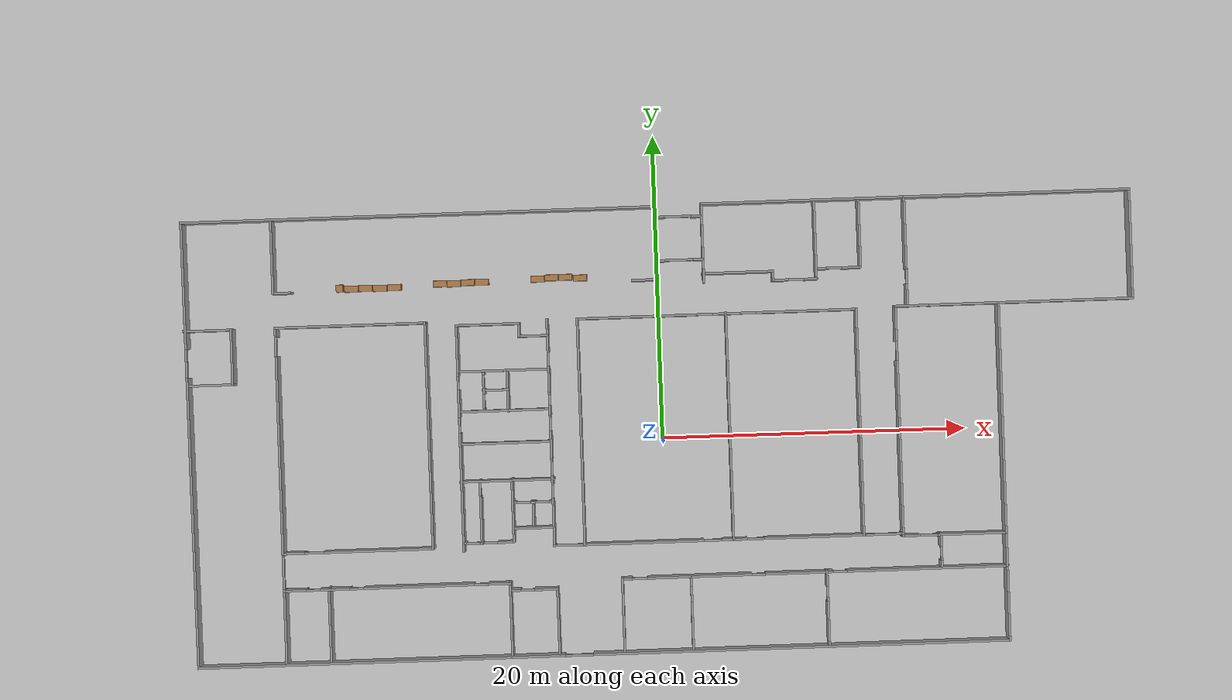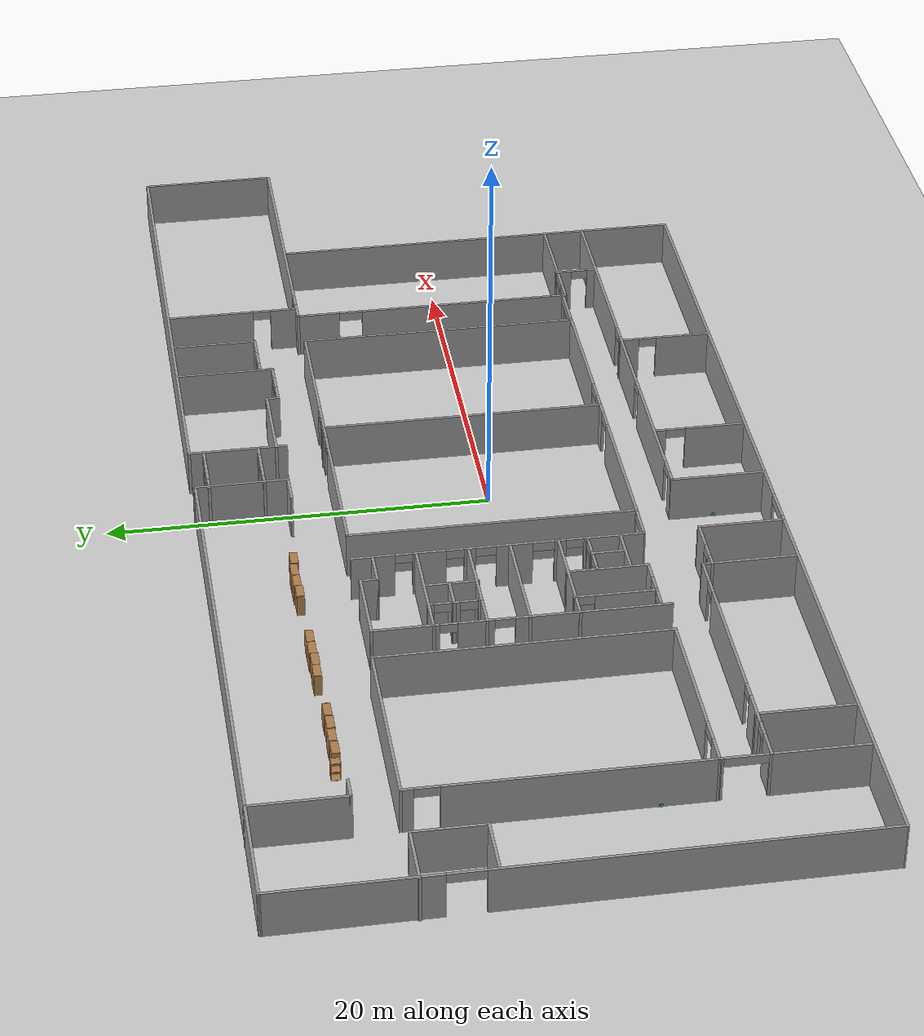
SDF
<sdf version="1.4">
 <world name="default">
  <light name="sun" type="directional">
   <pose>0 0 10 0 -0 0</pose>
   <diffuse>0.8 0.8 0.8 1</diffuse>
   <specular>0.2 0.2 0.2 1</specular>
   <attenuation>
    <range>1000</range>
    <constant>0.9</constant>
    <linear>0.01</linear>
    <quadratic>0.001</quadratic>
   </attenuation>
   <direction>-0.5 0.1 -0.9</direction>
  </light>
  <model name="ground_plane">
   <static>1</static>
   <link name="link">
    <collision name="collision">
     <geometry><plane><normal>0 0 1</normal><size>100 100</size></plane></geometry>
    </collision>
    <visual name="visual">
     <cast_shadows>0</cast_shadows>
     <geometry><plane><normal>0 0 1</normal><size>100 100</size></plane></geometry>
     <material>
      <script><uri>file://media/materials/scripts/gazebo.material</uri><name>Gazebo/Grey</name></script>
     </material>
    </visual>
    <velocity_decay><linear>0</linear><angular>0</angular></velocity_decay>
   </link>
  </model>
  <physics type="ode">
   <max_step_size>0.001</max_step_size>
   <real_time_factor>1</real_time_factor>
   <real_time_update_rate>1000</real_time_update_rate>
   <gravity>0 0 -9.8</gravity>
  </physics>
  <scene><ambient>0.4 0.4 0.4 1</ambient><background>0.7 0.7 0.7 1</background><shadows>1</shadows></scene>
  <spherical_coordinates>
   <surface_model>EARTH_WGS84</surface_model>
   <latitude_deg>0</latitude_deg>
   <longitude_deg>0</longitude_deg>
   <elevation>0</elevation>
   <heading_deg>0</heading_deg>
  </spherical_coordinates>
  <model name="Shannon">
   <pose>-0.0406 0.68299 0 0 -0 0</pose>
   <link name="Wall_10">
    <collision name="Wall_10_Collision">
     <geometry><box><size>22.25 0.15 2.5</size></box></geometry>
     <pose>0 0 1.25 0 -0 0</pose>
    </collision>
    <visual name="Wall_10_Visual">
     <pose>0 0 1.25 0 -0 0</pose>
     <geometry><box><size>22.25 0.15 2.5</size></box></geometry>
     <material>
      <script><uri>file://media/materials/scripts/gazebo.material</uri><name>Gazebo/Grey</name></script>
      <ambient>1 1 1 1</ambient>
     </material>
    </visual>
    <pose>22.3654 -3.62363 0 0 -0 -1.5708</pose>
    <velocity_decay><linear>0</linear><angular>0</angular></velocity_decay>
   </link>
   <link name="Wall_101">
    <pose>10.5074 -12.1568 0 0 -0 -1.5708</pose>
    <visual name="Wall_101_Visual_0">
     <pose>-1.95368 0 1.25 0 -0 0</pose>
     <geometry><box><size>1.09264 0.15 2.5</size></box></geometry>
     <material>
      <script><uri>file://media/materials/scripts/gazebo.material</uri><name>Gazebo/Grey</name></script>
      <ambient>1 1 1 1</ambient>
     </material>
    </visual>
    <collision name="Wall_101_Collision_0">
     <geometry><box><size>1.09264 0.15 2.5</size></box></geometry>
     <pose>-1.95368 0 1.25 0 -0 0</pose>
    </collision>
    <visual name="Wall_101_Visual_1">
     <pose>1.02674 0 1.25 0 -0 0</pose>
     <geometry><box><size>2.94652 0.15 2.5</size></box></geometry>
     <material>
      <script><uri>file://media/materials/scripts/gazebo.material</uri><name>Gazebo/Grey</name></script>
      <ambient>1 1 1 1</ambient>
     </material>
    </visual>
    <collision name="Wall_101_Collision_1">
     <geometry><box><size>2.94652 0.15 2.5</size></box></geometry>
     <pose>1.02674 0 1.25 0 -0 0</pose>
    </collision>
    <visual name="Wall_101_Visual_2">
     <pose>-0.926938 0 2.25 0 -0 0</pose>
     <geometry><box><size>0.960835 0.15 0.5</size></box></geometry>
     <material>
      <script><uri>file://media/materials/scripts/gazebo.material</uri><name>Gazebo/Grey</name></script>
      <ambient>1 1 1 1</ambient>
     </material>
    </visual>
    <collision name="Wall_101_Collision_2">
     <geometry><box><size>0.960835 0.15 0.5</size></box></geometry>
     <pose>-0.926938 0 2.25 0 -0 0</pose>
    </collision>
    <velocity_decay><linear>0</linear><angular>0</angular></velocity_decay>
   </link>
   <link name="Wall_103">
    <pose>-12.639 -7.09751 0 0 -0 3.14159</pose>
    <visual name="Wall_103_Visual_0">
     <pose>-0.521613 0 1.25 0 -0 0</pose>
     <geometry><box><size>0.206775 0.15 2.5</size></box></geometry>
     <material>
      <script><uri>file://media/materials/scripts/gazebo.material</uri><name>Gazebo/Grey</name></script>
      <ambient>1 1 1 1</ambient>
     </material>
    </visual>
    <collision name="Wall_103_Collision_0">
     <geometry><box><size>0.206775 0.15 2.5</size></box></geometry>
     <pose>-0.521613 0 1.25 0 -0 0</pose>
    </collision>
    <visual name="Wall_103_Visual_1">
     <pose>0.553387 0 1.25 0 -0 0</pose>
     <geometry><box><size>0.143225 0.15 2.5</size></box></geometry>
     <material>
      <script><uri>file://media/materials/scripts/gazebo.material</uri><name>Gazebo/Grey</name></script>
      <ambient>1 1 1 1</ambient>
     </material>
    </visual>
    <collision name="Wall_103_Collision_1">
     <geometry><box><size>0.143225 0.15 2.5</size></box></geometry>
     <pose>0.553387 0 1.25 0 -0 0</pose>
    </collision>
    <visual name="Wall_103_Visual_2">
     <pose>0.031775 0 2.25 0 -0 0</pose>
     <geometry><box><size>0.9 0.15 0.5</size></box></geometry>
     <material>
      <script><uri>file://media/materials/scripts/gazebo.material</uri><name>Gazebo/Grey</name></script>
      <ambient>1 1 1 1</ambient>
     </material>
    </visual>
    <collision name="Wall_103_Collision_2">
     <geometry><box><size>0.9 0.15 0.5</size></box></geometry>
     <pose>0.031775 0 2.25 0 -0 0</pose>
    </collision>
    <velocity_decay><linear>0</linear><angular>0</angular></velocity_decay>
   </link>
   <link name="Wall_108">
    <collision name="Wall_108_Collision">
     <geometry><box><size>3.75 0.15 2.5</size></box></geometry>
     <pose>0 0 1.25 0 -0 0</pose>
    </collision>
    <visual name="Wall_108_Visual">
     <pose>0 0 1.25 0 -0 0</pose>
     <geometry><box><size>3.75 0.15 2.5</size></box></geometry>
     <material>
      <script><uri>file://media/materials/scripts/gazebo.material</uri><name>Gazebo/Grey</name></script>
      <ambient>1 1 1 1</ambient>
     </material>
    </visual>
    <pose>-28.0998 5.68065 0 0 -0 -1.5708</pose>
    <velocity_decay><linear>0</linear><angular>0</angular></velocity_decay>
   </link>
   <link name="Wall_109">
    <collision name="Wall_109_Collision">
     <geometry><box><size>3 0.15 2.5</size></box></geometry>
     <pose>0 0 1.25 0 -0 0</pose>
    </collision>
    <visual name="Wall_109_Visual">
     <pose>0 0 1.25 0 -0 0</pose>
     <geometry><box><size>3 0.15 2.5</size></box></geometry>
     <material>
      <script><uri>file://media/materials/scripts/gazebo.material</uri><name>Gazebo/Grey</name></script>
      <ambient>1 1 1 1</ambient>
     </material>
    </visual>
    <pose>-29.5248 3.88065 0 0 -0 3.14159</pose>
    <velocity_decay><linear>0</linear><angular>0</angular></velocity_decay>
   </link>
   <link name="Wall_111">
    <pose>14.3103 -7.43874 0 0 -0 0</pose>
    <visual name="Wall_111_Visual_0">
     <pose>-1.26476 0 1.25 0 -0 0</pose>
     <geometry><box><size>0.220488 0.15 2.5</size></box></geometry>
     <material>
      <script><uri>file://media/materials/scripts/gazebo.material</uri><name>Gazebo/Grey</name></script>
      <ambient>1 1 1 1</ambient>
     </material>
    </visual>
    <collision name="Wall_111_Collision_0">
     <geometry><box><size>0.220488 0.15 2.5</size></box></geometry>
     <pose>-1.26476 0 1.25 0 -0 0</pose>
    </collision>
    <visual name="Wall_111_Visual_1">
     <pose>1.27845 0 1.25 0 -0 0</pose>
     <geometry><box><size>0.193101 0.15 2.5</size></box></geometry>
     <material>
      <script><uri>file://media/materials/scripts/gazebo.material</uri><name>Gazebo/Grey</name></script>
      <ambient>1 1 1 1</ambient>
     </material>
    </visual>
    <collision name="Wall_111_Collision_1">
     <geometry><box><size>0.193101 0.15 2.5</size></box></geometry>
     <pose>1.27845 0 1.25 0 -0 0</pose>
    </collision>
    <visual name="Wall_111_Visual_2">
     <pose>0.013694 0 2.25 0 -0 0</pose>
     <geometry><box><size>2.33641 0.15 0.5</size></box></geometry>
     <material>
      <script><uri>file://media/materials/scripts/gazebo.material</uri><name>Gazebo/Grey</name></script>
      <ambient>1 1 1 1</ambient>
     </material>
    </visual>
    <collision name="Wall_111_Collision_2">
     <geometry><box><size>2.33641 0.15 0.5</size></box></geometry>
     <pose>0.013694 0 2.25 0 -0 0</pose>
    </collision>
    <velocity_decay><linear>0</linear><angular>0</angular></velocity_decay>
   </link>
   <link name="Wall_113">
    <pose>-6.33435 -7.42718 0 0 -0 3.12996</pose>
    <visual name="Wall_113_Visual_0">
     <pose>-0.982605 0 1.25 0 -0 0</pose>
     <geometry><box><size>0.174156 0.15 2.5</size></box></geometry>
     <material>
      <script><uri>file://media/materials/scripts/gazebo.material</uri><name>Gazebo/Grey</name></script>
      <ambient>1 1 1 1</ambient>
     </material>
    </visual>
    <collision name="Wall_113_Collision_0">
     <geometry><box><size>0.174156 0.15 2.5</size></box></geometry>
     <pose>-0.982605 0 1.25 0 -0 0</pose>
    </collision>
    <visual name="Wall_113_Visual_1">
     <pose>0.989375 0 1.25 0 -0 0</pose>
     <geometry><box><size>0.160617 0.15 2.5</size></box></geometry>
     <material>
      <script><uri>file://media/materials/scripts/gazebo.material</uri><name>Gazebo/Grey</name></script>
      <ambient>1 1 1 1</ambient>
     </material>
    </visual>
    <collision name="Wall_113_Collision_1">
     <geometry><box><size>0.160617 0.15 2.5</size></box></geometry>
     <pose>0.989375 0 1.25 0 -0 0</pose>
    </collision>
    <visual name="Wall_113_Visual_2">
     <pose>0.00677 0 2.25 0 -0 0</pose>
     <geometry><box><size>1.80459 0.15 0.5</size></box></geometry>
     <material>
      <script><uri>file://media/materials/scripts/gazebo.material</uri><name>Gazebo/Grey</name></script>
      <ambient>1 1 1 1</ambient>
     </material>
    </visual>
    <collision name="Wall_113_Collision_2">
     <geometry><box><size>1.80459 0.15 0.5</size></box></geometry>
     <pose>0.00677 0 2.25 0 -0 0</pose>
    </collision>
    <velocity_decay><linear>0</linear><angular>0</angular></velocity_decay>
   </link>
   <link name="Wall_115">
    <pose>-25.1881 -8.57974 0 0 -0 1.57264</pose>
    <visual name="Wall_115_Visual_0">
     <pose>-1.20863 0 1.25 0 -0 0</pose>
     <geometry><box><size>0.183947 0.15 2.5</size></box></geometry>
     <material>
      <script><uri>file://media/materials/scripts/gazebo.material</uri><name>Gazebo/Grey</name></script>
      <ambient>1 1 1 1</ambient>
     </material>
    </visual>
    <collision name="Wall_115_Collision_0">
     <geometry><box><size>0.183947 0.15 2.5</size></box></geometry>
     <pose>-1.20863 0 1.25 0 -0 0</pose>
    </collision>
    <visual name="Wall_115_Visual_1">
     <pose>1.16989 0 1.25 0 -0 0</pose>
     <geometry><box><size>0.261435 0.15 2.5</size></box></geometry>
     <material>
      <script><uri>file://media/materials/scripts/gazebo.material</uri><name>Gazebo/Grey</name></script>
      <ambient>1 1 1 1</ambient>
     </material>
    </visual>
    <collision name="Wall_115_Collision_1">
     <geometry><box><size>0.261435 0.15 2.5</size></box></geometry>
     <pose>1.16989 0 1.25 0 -0 0</pose>
    </collision>
    <visual name="Wall_115_Visual_2">
     <pose>-0.038744 0 2.25 0 -0 0</pose>
     <geometry><box><size>2.15582 0.15 0.5</size></box></geometry>
     <material>
      <script><uri>file://media/materials/scripts/gazebo.material</uri><name>Gazebo/Grey</name></script>
      <ambient>1 1 1 1</ambient>
     </material>
    </visual>
    <collision name="Wall_115_Collision_2">
     <geometry><box><size>2.15582 0.15 0.5</size></box></geometry>
     <pose>-0.038744 0 2.25 0 -0 0</pose>
    </collision>
    <velocity_decay><linear>0</linear><angular>0</angular></velocity_decay>
   </link>
   <link name="Wall_118">
    <collision name="Wall_118_Collision">
     <geometry><box><size>31.25 0.15 2.5</size></box></geometry>
     <pose>0 0 1.25 0 -0 0</pose>
    </collision>
    <visual name="Wall_118_Visual">
     <pose>0 0 1.25 0 -0 0</pose>
     <geometry><box><size>31.25 0.15 2.5</size></box></geometry>
     <material>
      <script><uri>file://media/materials/scripts/gazebo.material</uri><name>Gazebo/Grey</name></script>
      <ambient>1 1 1 1</ambient>
     </material>
    </visual>
    <pose>-15.6004 14.61 0 0 -0 0</pose>
    <velocity_decay><linear>0</linear><angular>0</angular></velocity_decay>
   </link>
   <link name="Wall_12">
    <pose>-4.30964 -14.6736 0 0 -0 3.14159</pose>
    <visual name="Wall_12_Visual_0">
     <pose>-13.02 0 1.25 0 -0 0</pose>
     <geometry><box><size>27.46 0.15 2.5</size></box></geometry>
     <material>
      <script><uri>file://media/materials/scripts/gazebo.material</uri><name>Gazebo/Grey</name></script>
      <ambient>1 1 1 1</ambient>
     </material>
    </visual>
    <collision name="Wall_12_Collision_0">
     <geometry><box><size>27.46 0.15 2.5</size></box></geometry>
     <pose>-13.02 0 1.25 0 -0 0</pose>
    </collision>
    <visual name="Wall_12_Visual_1">
     <pose>14.6599 0 1.25 0 -0 0</pose>
     <geometry><box><size>24.1801 0.15 2.5</size></box></geometry>
     <material>
      <script><uri>file://media/materials/scripts/gazebo.material</uri><name>Gazebo/Grey</name></script>
      <ambient>1 1 1 1</ambient>
     </material>
    </visual>
    <collision name="Wall_12_Collision_1">
     <geometry><box><size>24.1801 0.15 2.5</size></box></geometry>
     <pose>14.6599 0 1.25 0 -0 0</pose>
    </collision>
    <visual name="Wall_12_Visual_2">
     <pose>1.63993 0 2.25 0 -0 0</pose>
     <geometry><box><size>1.85983 0.15 0.5</size></box></geometry>
     <material>
      <script><uri>file://media/materials/scripts/gazebo.material</uri><name>Gazebo/Grey</name></script>
      <ambient>1 1 1 1</ambient>
     </material>
    </visual>
    <collision name="Wall_12_Collision_2">
     <geometry><box><size>1.85983 0.15 0.5</size></box></geometry>
     <pose>1.63993 0 2.25 0 -0 0</pose>
    </collision>
    <velocity_decay><linear>0</linear><angular>0</angular></velocity_decay>
   </link>
   <link name="Wall_120">
    <collision name="Wall_120_Collision">
     <geometry><box><size>28.25 0.15 2.5</size></box></geometry>
     <pose>0 0 1.25 0 -0 0</pose>
    </collision>
    <visual name="Wall_120_Visual">
     <pose>0 0 1.25 0 -0 0</pose>
     <geometry><box><size>28.25 0.15 2.5</size></box></geometry>
     <material>
      <script><uri>file://media/materials/scripts/gazebo.material</uri><name>Gazebo/Grey</name></script>
      <ambient>1 1 1 1</ambient>
     </material>
    </visual>
    <pose>17.1298 14.6743 0 0 -0 0</pose>
    <velocity_decay><linear>0</linear><angular>0</angular></velocity_decay>
   </link>
   <link name="Wall_122">
    <pose>1.42965 13.9029 0 0 -0 0</pose>
    <visual name="Wall_122_Visual_0">
     <pose>-1.23095 0 1.25 0 -0 0</pose>
     <geometry><box><size>0.788098 0.15 2.5</size></box></geometry>
     <material>
      <script><uri>file://media/materials/scripts/gazebo.material</uri><name>Gazebo/Grey</name></script>
      <ambient>1 1 1 1</ambient>
     </material>
    </visual>
    <collision name="Wall_122_Collision_0">
     <geometry><box><size>0.788098 0.15 2.5</size></box></geometry>
     <pose>-1.23095 0 1.25 0 -0 0</pose>
    </collision>
    <visual name="Wall_122_Visual_1">
     <pose>1.28137 0 1.25 0 -0 0</pose>
     <geometry><box><size>0.687253 0.15 2.5</size></box></geometry>
     <material>
      <script><uri>file://media/materials/scripts/gazebo.material</uri><name>Gazebo/Grey</name></script>
      <ambient>1 1 1 1</ambient>
     </material>
    </visual>
    <collision name="Wall_122_Collision_1">
     <geometry><box><size>0.687253 0.15 2.5</size></box></geometry>
     <pose>1.28137 0 1.25 0 -0 0</pose>
    </collision>
    <visual name="Wall_122_Visual_2">
     <pose>0.050423 0 2.25 0 -0 0</pose>
     <geometry><box><size>1.77465 0.15 0.5</size></box></geometry>
     <material>
      <script><uri>file://media/materials/scripts/gazebo.material</uri><name>Gazebo/Grey</name></script>
      <ambient>1 1 1 1</ambient>
     </material>
    </visual>
    <collision name="Wall_122_Collision_2">
     <geometry><box><size>1.77465 0.15 0.5</size></box></geometry>
     <pose>0.050423 0 2.25 0 -0 0</pose>
    </collision>
    <velocity_decay><linear>0</linear><angular>0</angular></velocity_decay>
   </link>
   <link name="Wall_14">
    <pose>-31.0675 -0.031809 0 0 -0 1.57646</pose>
    <visual name="Wall_14_Visual_0">
     <pose>-5.13073 0 1.25 0 -0 0</pose>
     <geometry><box><size>19.1731 0.15 2.5</size></box></geometry>
     <material>
      <script><uri>file://media/materials/scripts/gazebo.material</uri><name>Gazebo/Grey</name></script>
      <ambient>1 1 1 1</ambient>
     </material>
    </visual>
    <collision name="Wall_14_Collision_0">
     <geometry><box><size>19.1731 0.15 2.5</size></box></geometry>
     <pose>-5.13073 0 1.25 0 -0 0</pose>
    </collision>
    <visual name="Wall_14_Visual_1">
     <pose>10.5202 0 1.25 0 -0 0</pose>
     <geometry><box><size>8.3942 0.15 2.5</size></box></geometry>
     <material>
      <script><uri>file://media/materials/scripts/gazebo.material</uri><name>Gazebo/Grey</name></script>
      <ambient>1 1 1 1</ambient>
     </material>
    </visual>
    <collision name="Wall_14_Collision_1">
     <geometry><box><size>8.3942 0.15 2.5</size></box></geometry>
     <pose>10.5202 0 1.25 0 -0 0</pose>
    </collision>
    <visual name="Wall_14_Visual_2">
     <pose>5.38944 0 2.25 0 -0 0</pose>
     <geometry><box><size>1.86726 0.15 0.5</size></box></geometry>
     <material>
      <script><uri>file://media/materials/scripts/gazebo.material</uri><name>Gazebo/Grey</name></script>
      <ambient>1 1 1 1</ambient>
     </material>
    </visual>
    <collision name="Wall_14_Collision_2">
     <geometry><box><size>1.86726 0.15 0.5</size></box></geometry>
     <pose>5.38944 0 2.25 0 -0 0</pose>
    </collision>
    <velocity_decay><linear>0</linear><angular>0</angular></velocity_decay>
   </link>
   <link name="Wall_16">
    <collision name="Wall_16_Collision">
     <geometry><box><size>10 0.15 2.5</size></box></geometry>
     <pose>0 0 1.25 0 -0 0</pose>
    </collision>
    <visual name="Wall_16_Visual">
     <pose>0 0 1.25 0 -0 0</pose>
     <geometry><box><size>10 0.15 2.5</size></box></geometry>
     <material>
      <script><uri>file://media/materials/scripts/gazebo.material</uri><name>Gazebo/Grey</name></script>
      <ambient>1 1 1 1</ambient>
     </material>
    </visual>
    <pose>-20.2786 7.49586 0 0 -0 0</pose>
    <velocity_decay><linear>0</linear><angular>0</angular></velocity_decay>
   </link>
   <link name="Wall_17">
    <collision name="Wall_17_Collision">
     <geometry><box><size>15 0.15 2.5</size></box></geometry>
     <pose>0 0 1.25 0 -0 0</pose>
    </collision>
    <visual name="Wall_17_Visual">
     <pose>0 0 1.25 0 -0 0</pose>
     <geometry><box><size>15 0.15 2.5</size></box></geometry>
     <material>
      <script><uri>file://media/materials/scripts/gazebo.material</uri><name>Gazebo/Grey</name></script>
      <ambient>1 1 1 1</ambient>
     </material>
    </visual>
    <pose>-15.3403 0.07086 0 0 -0 -1.569</pose>
    <velocity_decay><linear>0</linear><angular>0</angular></velocity_decay>
   </link>
   <link name="Wall_18">
    <pose>-20.2653 -7.35414 0 0 -0 3.14159</pose>
    <visual name="Wall_18_Visual_0">
     <pose>-1.3866 0 1.25 0 -0 0</pose>
     <geometry><box><size>7.2268 0.15 2.5</size></box></geometry>
     <material>
      <script><uri>file://media/materials/scripts/gazebo.material</uri><name>Gazebo/Grey</name></script>
      <ambient>1 1 1 1</ambient>
     </material>
    </visual>
    <collision name="Wall_18_Collision_0">
     <geometry><box><size>7.2268 0.15 2.5</size></box></geometry>
     <pose>-1.3866 0 1.25 0 -0 0</pose>
    </collision>
    <visual name="Wall_18_Visual_1">
     <pose>4.24845 0 1.25 0 -0 0</pose>
     <geometry><box><size>1.50311 0.15 2.5</size></box></geometry>
     <material>
      <script><uri>file://media/materials/scripts/gazebo.material</uri><name>Gazebo/Grey</name></script>
      <ambient>1 1 1 1</ambient>
     </material>
    </visual>
    <collision name="Wall_18_Collision_1">
     <geometry><box><size>1.50311 0.15 2.5</size></box></geometry>
     <pose>4.24845 0 1.25 0 -0 0</pose>
    </collision>
    <visual name="Wall_18_Visual_2">
     <pose>2.86185 0 2.25 0 -0 0</pose>
     <geometry><box><size>1.27009 0.15 0.5</size></box></geometry>
     <material>
      <script><uri>file://media/materials/scripts/gazebo.material</uri><name>Gazebo/Grey</name></script>
      <ambient>1 1 1 1</ambient>
     </material>
    </visual>
    <collision name="Wall_18_Collision_2">
     <geometry><box><size>1.27009 0.15 0.5</size></box></geometry>
     <pose>2.86185 0 2.25 0 -0 0</pose>
    </collision>
    <velocity_decay><linear>0</linear><angular>0</angular></velocity_decay>
   </link>
   <link name="Wall_20">
    <pose>-25.1903 0.07086 0 0 -0 1.5708</pose>
    <visual name="Wall_20_Visual_0">
     <pose>-0.95824 0 1.25 0 -0 0</pose>
     <geometry><box><size>13.0835 0.15 2.5</size></box></geometry>
     <material>
      <script><uri>file://media/materials/scripts/gazebo.material</uri><name>Gazebo/Grey</name></script>
      <ambient>1 1 1 1</ambient>
     </material>
    </visual>
    <collision name="Wall_20_Collision_0">
     <geometry><box><size>13.0835 0.15 2.5</size></box></geometry>
     <pose>-0.95824 0 1.25 0 -0 0</pose>
    </collision>
    <visual name="Wall_20_Visual_1">
     <pose>7.16524 0 1.25 0 -0 0</pose>
     <geometry><box><size>0.669521 0.15 2.5</size></box></geometry>
     <material>
      <script><uri>file://media/materials/scripts/gazebo.material</uri><name>Gazebo/Grey</name></script>
      <ambient>1 1 1 1</ambient>
     </material>
    </visual>
    <collision name="Wall_20_Collision_1">
     <geometry><box><size>0.669521 0.15 2.5</size></box></geometry>
     <pose>7.16524 0 1.25 0 -0 0</pose>
    </collision>
    <visual name="Wall_20_Visual_2">
     <pose>6.207 0 2.25 0 -0 0</pose>
     <geometry><box><size>1.24696 0.15 0.5</size></box></geometry>
     <material>
      <script><uri>file://media/materials/scripts/gazebo.material</uri><name>Gazebo/Grey</name></script>
      <ambient>1 1 1 1</ambient>
     </material>
    </visual>
    <collision name="Wall_20_Collision_2">
     <geometry><box><size>1.24696 0.15 0.5</size></box></geometry>
     <pose>6.207 0 2.25 0 -0 0</pose>
    </collision>
    <velocity_decay><linear>0</linear><angular>0</angular></velocity_decay>
   </link>
   <link name="Wall_22">
    <collision name="Wall_22_Collision">
     <geometry><box><size>5 0.15 2.5</size></box></geometry>
     <pose>0 0 1.25 0 -0 0</pose>
    </collision>
    <visual name="Wall_22_Visual">
     <pose>0 0 1.25 0 -0 0</pose>
     <geometry><box><size>5 0.15 2.5</size></box></geometry>
     <material>
      <script><uri>file://media/materials/scripts/gazebo.material</uri><name>Gazebo/Grey</name></script>
      <ambient>1 1 1 1</ambient>
     </material>
    </visual>
    <pose>-25.1858 -12.2303 0 0 -0 1.5708</pose>
    <velocity_decay><linear>0</linear><angular>0</angular></velocity_decay>
   </link>
   <link name="Wall_23">
    <pose>-17.7608 -9.80534 0 0 -0 0</pose>
    <visual name="Wall_23_Visual_0">
     <pose>-6.73914 0 1.25 0 -0 0</pose>
     <geometry><box><size>1.52171 0.15 2.5</size></box></geometry>
     <material>
      <script><uri>file://media/materials/scripts/gazebo.material</uri><name>Gazebo/Grey</name></script>
      <ambient>1 1 1 1</ambient>
     </material>
    </visual>
    <collision name="Wall_23_Collision_0">
     <geometry><box><size>1.52171 0.15 2.5</size></box></geometry>
     <pose>-6.73914 0 1.25 0 -0 0</pose>
    </collision>
    <visual name="Wall_23_Visual_1">
     <pose>-4.09419 0 1.25 0 -0 0</pose>
     <geometry><box><size>1.96819 0.15 2.5</size></box></geometry>
     <material>
      <script><uri>file://media/materials/scripts/gazebo.material</uri><name>Gazebo/Grey</name></script>
      <ambient>1 1 1 1</ambient>
     </material>
    </visual>
    <collision name="Wall_23_Collision_1">
     <geometry><box><size>1.96819 0.15 2.5</size></box></geometry>
     <pose>-4.09419 0 1.25 0 -0 0</pose>
    </collision>
    <visual name="Wall_23_Visual_2">
     <pose>1.43402 0 1.25 0 -0 0</pose>
     <geometry><box><size>7.28824 0.15 2.5</size></box></geometry>
     <material>
      <script><uri>file://media/materials/scripts/gazebo.material</uri><name>Gazebo/Grey</name></script>
      <ambient>1 1 1 1</ambient>
     </material>
    </visual>
    <collision name="Wall_23_Collision_2">
     <geometry><box><size>7.28824 0.15 2.5</size></box></geometry>
     <pose>1.43402 0 1.25 0 -0 0</pose>
    </collision>
    <visual name="Wall_23_Visual_3">
     <pose>6.73907 0 1.25 0 -0 0</pose>
     <geometry><box><size>1.52186 0.15 2.5</size></box></geometry>
     <material>
      <script><uri>file://media/materials/scripts/gazebo.material</uri><name>Gazebo/Grey</name></script>
      <ambient>1 1 1 1</ambient>
     </material>
    </visual>
    <collision name="Wall_23_Collision_3">
     <geometry><box><size>1.52186 0.15 2.5</size></box></geometry>
     <pose>6.73907 0 1.25 0 -0 0</pose>
    </collision>
    <visual name="Wall_23_Visual_4">
     <pose>-5.52829 0 2.25 0 -0 0</pose>
     <geometry><box><size>0.9 0.15 0.5</size></box></geometry>
     <material>
      <script><uri>file://media/materials/scripts/gazebo.material</uri><name>Gazebo/Grey</name></script>
      <ambient>1 1 1 1</ambient>
     </material>
    </visual>
    <collision name="Wall_23_Collision_4">
     <geometry><box><size>0.9 0.15 0.5</size></box></geometry>
     <pose>-5.52829 0 2.25 0 -0 0</pose>
    </collision>
    <visual name="Wall_23_Visual_5">
     <pose>-2.6601 0 2.25 0 -0 0</pose>
     <geometry><box><size>0.9 0.15 0.5</size></box></geometry>
     <material>
      <script><uri>file://media/materials/scripts/gazebo.material</uri><name>Gazebo/Grey</name></script>
      <ambient>1 1 1 1</ambient>
     </material>
    </visual>
    <collision name="Wall_23_Collision_5">
     <geometry><box><size>0.9 0.15 0.5</size></box></geometry>
     <pose>-2.6601 0 2.25 0 -0 0</pose>
    </collision>
    <visual name="Wall_23_Visual_6">
     <pose>5.52814 0 2.25 0 -0 0</pose>
     <geometry><box><size>0.9 0.15 0.5</size></box></geometry>
     <material>
      <script><uri>file://media/materials/scripts/gazebo.material</uri><name>Gazebo/Grey</name></script>
      <ambient>1 1 1 1</ambient>
     </material>
    </visual>
    <collision name="Wall_23_Collision_6">
     <geometry><box><size>0.9 0.15 0.5</size></box></geometry>
     <pose>5.52814 0 2.25 0 -0 0</pose>
    </collision>
    <velocity_decay><linear>0</linear><angular>0</angular></velocity_decay>
   </link>
   <link name="Wall_24">
    <collision name="Wall_24_Collision">
     <geometry><box><size>5 0.15 2.5</size></box></geometry>
     <pose>0 0 1.25 0 -0 0</pose>
    </collision>
    <visual name="Wall_24_Visual">
     <pose>0 0 1.25 0 -0 0</pose>
     <geometry><box><size>5 0.15 2.5</size></box></geometry>
     <material>
      <script><uri>file://media/materials/scripts/gazebo.material</uri><name>Gazebo/Grey</name></script>
      <ambient>1 1 1 1</ambient>
     </material>
    </visual>
    <pose>-10.3358 -12.2303 0 0 -0 -1.5708</pose>
    <velocity_decay><linear>0</linear><angular>0</angular></velocity_decay>
   </link>
   <link name="Wall_26">
    <pose>-8.78595 -10.2837 0 0 -0 0</pose>
    <visual name="Wall_26_Visual_0">
     <pose>-1.2458 0 1.25 0 -0 0</pose>
     <geometry><box><size>0.7584 0.15 2.5</size></box></geometry>
     <material>
      <script><uri>file://media/materials/scripts/gazebo.material</uri><name>Gazebo/Grey</name></script>
      <ambient>1 1 1 1</ambient>
     </material>
    </visual>
    <collision name="Wall_26_Collision_0">
     <geometry><box><size>0.7584 0.15 2.5</size></box></geometry>
     <pose>-1.2458 0 1.25 0 -0 0</pose>
    </collision>
    <visual name="Wall_26_Visual_1">
     <pose>0.8292 0 1.25 0 -0 0</pose>
     <geometry><box><size>1.5916 0.15 2.5</size></box></geometry>
     <material>
      <script><uri>file://media/materials/scripts/gazebo.material</uri><name>Gazebo/Grey</name></script>
      <ambient>1 1 1 1</ambient>
     </material>
    </visual>
    <collision name="Wall_26_Collision_1">
     <geometry><box><size>1.5916 0.15 2.5</size></box></geometry>
     <pose>0.8292 0 1.25 0 -0 0</pose>
    </collision>
    <visual name="Wall_26_Visual_2">
     <pose>-0.4166 0 2.25 0 -0 0</pose>
     <geometry><box><size>0.9 0.15 0.5</size></box></geometry>
     <material>
      <script><uri>file://media/materials/scripts/gazebo.material</uri><name>Gazebo/Grey</name></script>
      <ambient>1 1 1 1</ambient>
     </material>
    </visual>
    <collision name="Wall_26_Collision_2">
     <geometry><box><size>0.9 0.15 0.5</size></box></geometry>
     <pose>-0.4166 0 2.25 0 -0 0</pose>
    </collision>
    <velocity_decay><linear>0</linear><angular>0</angular></velocity_decay>
   </link>
   <link name="Wall_27">
    <collision name="Wall_27_Collision">
     <geometry><box><size>4.5 0.15 2.5</size></box></geometry>
     <pose>0 0 1.25 0 -0 0</pose>
    </collision>
    <visual name="Wall_27_Visual">
     <pose>0 0 1.25 0 -0 0</pose>
     <geometry><box><size>4.5 0.15 2.5</size></box></geometry>
     <material>
      <script><uri>file://media/materials/scripts/gazebo.material</uri><name>Gazebo/Grey</name></script>
      <ambient>1 1 1 1</ambient>
     </material>
    </visual>
    <pose>-7.23595 -12.4587 0 0 -0 -1.5708</pose>
    <velocity_decay><linear>0</linear><angular>0</angular></velocity_decay>
   </link>
   <link name="Wall_29">
    <collision name="Wall_29_Collision">
     <geometry><box><size>5 0.15 2.5</size></box></geometry>
     <pose>0 0 1.25 0 -0 0</pose>
    </collision>
    <visual name="Wall_29_Visual">
     <pose>0 0 1.25 0 -0 0</pose>
     <geometry><box><size>5 0.15 2.5</size></box></geometry>
     <material>
      <script><uri>file://media/materials/scripts/gazebo.material</uri><name>Gazebo/Grey</name></script>
      <ambient>1 1 1 1</ambient>
     </material>
    </visual>
    <pose>-2.95728 -12.2072 0 0 -0 1.5708</pose>
    <velocity_decay><linear>0</linear><angular>0</angular></velocity_decay>
   </link>
   <link name="Wall_3">
    <collision name="Wall_3_Collision">
     <geometry><box><size>7.25 0.15 2.5</size></box></geometry>
     <pose>0 0 1.25 0 -0 0</pose>
    </collision>
    <visual name="Wall_3_Visual">
     <pose>0 0 1.25 0 -0 0</pose>
     <geometry><box><size>7.25 0.15 2.5</size></box></geometry>
     <material>
      <script><uri>file://media/materials/scripts/gazebo.material</uri><name>Gazebo/Grey</name></script>
      <ambient>1 1 1 1</ambient>
     </material>
    </visual>
    <pose>31.1997 11.0602 0 0 -0 -1.57077</pose>
    <velocity_decay><linear>0</linear><angular>0</angular></velocity_decay>
   </link>
   <link name="Wall_30">
    <pose>9.71772 -9.78221 0 0 -0 0</pose>
    <visual name="Wall_30_Visual_0">
     <pose>-12.3837 0 1.25 0 -0 0</pose>
     <geometry><box><size>0.732546 0.15 2.5</size></box></geometry>
     <material>
      <script><uri>file://media/materials/scripts/gazebo.material</uri><name>Gazebo/Grey</name></script>
      <ambient>1 1 1 1</ambient>
     </material>
    </visual>
    <collision name="Wall_30_Collision_0">
     <geometry><box><size>0.732546 0.15 2.5</size></box></geometry>
     <pose>-12.3837 0 1.25 0 -0 0</pose>
    </collision>
    <visual name="Wall_30_Visual_1">
     <pose>-7.59417 0 1.25 0 -0 0</pose>
     <geometry><box><size>6.86407 0.15 2.5</size></box></geometry>
     <material>
      <script><uri>file://media/materials/scripts/gazebo.material</uri><name>Gazebo/Grey</name></script>
      <ambient>1 1 1 1</ambient>
     </material>
    </visual>
    <collision name="Wall_30_Collision_1">
     <geometry><box><size>6.86407 0.15 2.5</size></box></geometry>
     <pose>-7.59417 0 1.25 0 -0 0</pose>
    </collision>
    <visual name="Wall_30_Visual_2">
     <pose>-1.03326 0 1.25 0 -0 0</pose>
     <geometry><box><size>4.45774 0.15 2.5</size></box></geometry>
     <material>
      <script><uri>file://media/materials/scripts/gazebo.material</uri><name>Gazebo/Grey</name></script>
      <ambient>1 1 1 1</ambient>
     </material>
    </visual>
    <collision name="Wall_30_Collision_2">
     <geometry><box><size>4.45774 0.15 2.5</size></box></geometry>
     <pose>-1.03326 0 1.25 0 -0 0</pose>
    </collision>
    <visual name="Wall_30_Visual_3">
     <pose>7.42281 0 1.25 0 -0 0</pose>
     <geometry><box><size>10.6544 0.15 2.5</size></box></geometry>
     <material>
      <script><uri>file://media/materials/scripts/gazebo.material</uri><name>Gazebo/Grey</name></script>
      <ambient>1 1 1 1</ambient>
     </material>
    </visual>
    <collision name="Wall_30_Collision_3">
     <geometry><box><size>10.6544 0.15 2.5</size></box></geometry>
     <pose>7.42281 0 1.25 0 -0 0</pose>
    </collision>
    <visual name="Wall_30_Visual_4">
     <pose>-11.5218 0 2.25 0 -0 0</pose>
     <geometry><box><size>0.991253 0.15 0.5</size></box></geometry>
     <material>
      <script><uri>file://media/materials/scripts/gazebo.material</uri><name>Gazebo/Grey</name></script>
      <ambient>1 1 1 1</ambient>
     </material>
    </visual>
    <collision name="Wall_30_Collision_4">
     <geometry><box><size>0.991253 0.15 0.5</size></box></geometry>
     <pose>-11.5218 0 2.25 0 -0 0</pose>
    </collision>
    <visual name="Wall_30_Visual_5">
     <pose>-3.71213 0 2.25 0 -0 0</pose>
     <geometry><box><size>0.9 0.15 0.5</size></box></geometry>
     <material>
      <script><uri>file://media/materials/scripts/gazebo.material</uri><name>Gazebo/Grey</name></script>
      <ambient>1 1 1 1</ambient>
     </material>
    </visual>
    <collision name="Wall_30_Collision_5">
     <geometry><box><size>0.9 0.15 0.5</size></box></geometry>
     <pose>-3.71213 0 2.25 0 -0 0</pose>
    </collision>
    <visual name="Wall_30_Visual_6">
     <pose>1.64561 0 2.25 0 -0 0</pose>
     <geometry><box><size>0.9 0.15 0.5</size></box></geometry>
     <material>
      <script><uri>file://media/materials/scripts/gazebo.material</uri><name>Gazebo/Grey</name></script>
      <ambient>1 1 1 1</ambient>
     </material>
    </visual>
    <collision name="Wall_30_Collision_6">
     <geometry><box><size>0.9 0.15 0.5</size></box></geometry>
     <pose>1.64561 0 2.25 0 -0 0</pose>
    </collision>
    <velocity_decay><linear>0</linear><angular>0</angular></velocity_decay>
   </link>
   <link name="Wall_32">
    <collision name="Wall_32_Collision">
     <geometry><box><size>5 0.15 2.5</size></box></geometry>
     <pose>0 0 1.25 0 -0 0</pose>
    </collision>
    <visual name="Wall_32_Visual">
     <pose>0 0 1.25 0 -0 0</pose>
     <geometry><box><size>5 0.15 2.5</size></box></geometry>
     <material>
      <script><uri>file://media/materials/scripts/gazebo.material</uri><name>Gazebo/Grey</name></script>
      <ambient>1 1 1 1</ambient>
     </material>
    </visual>
    <pose>-22.2482 -12.1767 0 0 -0 -1.5708</pose>
    <velocity_decay><linear>0</linear><angular>0</angular></velocity_decay>
   </link>
   <link name="Wall_34">
    <pose>3.83527 7.41126 0 0 -0 0</pose>
    <visual name="Wall_34_Visual_0">
     <pose>-5.27347 0 1.25 0 -0 0</pose>
     <geometry><box><size>7.95306 0.15 2.5</size></box></geometry>
     <material>
      <script><uri>file://media/materials/scripts/gazebo.material</uri><name>Gazebo/Grey</name></script>
      <ambient>1 1 1 1</ambient>
     </material>
    </visual>
    <collision name="Wall_34_Collision_0">
     <geometry><box><size>7.95306 0.15 2.5</size></box></geometry>
     <pose>-5.27347 0 1.25 0 -0 0</pose>
    </collision>
    <visual name="Wall_34_Visual_1">
     <pose>0.653062 0 1.25 0 -0 0</pose>
     <geometry><box><size>1.78 0.15 2.5</size></box></geometry>
     <material>
      <script><uri>file://media/materials/scripts/gazebo.material</uri><name>Gazebo/Grey</name></script>
      <ambient>1 1 1 1</ambient>
     </material>
    </visual>
    <collision name="Wall_34_Collision_1">
     <geometry><box><size>1.78 0.15 2.5</size></box></geometry>
     <pose>0.653062 0 1.25 0 -0 0</pose>
    </collision>
    <visual name="Wall_34_Visual_2">
     <pose>5.91653 0 1.25 0 -0 0</pose>
     <geometry><box><size>6.66694 0.15 2.5</size></box></geometry>
     <material>
      <script><uri>file://media/materials/scripts/gazebo.material</uri><name>Gazebo/Grey</name></script>
      <ambient>1 1 1 1</ambient>
     </material>
    </visual>
    <collision name="Wall_34_Collision_2">
     <geometry><box><size>6.66694 0.15 2.5</size></box></geometry>
     <pose>5.91653 0 1.25 0 -0 0</pose>
    </collision>
    <visual name="Wall_34_Visual_3">
     <pose>-0.766938 0 2.25 0 -0 0</pose>
     <geometry><box><size>1.06 0.15 0.5</size></box></geometry>
     <material>
      <script><uri>file://media/materials/scripts/gazebo.material</uri><name>Gazebo/Grey</name></script>
      <ambient>1 1 1 1</ambient>
     </material>
    </visual>
    <collision name="Wall_34_Collision_3">
     <geometry><box><size>1.06 0.15 0.5</size></box></geometry>
     <pose>-0.766938 0 2.25 0 -0 0</pose>
    </collision>
    <visual name="Wall_34_Visual_4">
     <pose>2.06306 0 2.25 0 -0 0</pose>
     <geometry><box><size>1.04 0.15 0.5</size></box></geometry>
     <material>
      <script><uri>file://media/materials/scripts/gazebo.material</uri><name>Gazebo/Grey</name></script>
      <ambient>1 1 1 1</ambient>
     </material>
    </visual>
    <collision name="Wall_34_Collision_4">
     <geometry><box><size>1.04 0.15 0.5</size></box></geometry>
     <pose>2.06306 0 2.25 0 -0 0</pose>
    </collision>
    <velocity_decay><linear>0</linear><angular>0</angular></velocity_decay>
   </link>
   <link name="Wall_35">
    <collision name="Wall_35_Collision">
     <geometry><box><size>15 0.15 2.5</size></box></geometry>
     <pose>0 0 1.25 0 -0 0</pose>
    </collision>
    <visual name="Wall_35_Visual">
     <pose>0 0 1.25 0 -0 0</pose>
     <geometry><box><size>15 0.15 2.5</size></box></geometry>
     <material>
      <script><uri>file://media/materials/scripts/gazebo.material</uri><name>Gazebo/Grey</name></script>
      <ambient>1 1 1 1</ambient>
     </material>
    </visual>
    <pose>13.0103 -0.013741 0 0 -0 -1.5708</pose>
    <velocity_decay><linear>0</linear><angular>0</angular></velocity_decay>
   </link>
   <link name="Wall_36">
    <pose>3.83527 -7.43874 0 0 -0 3.14159</pose>
    <visual name="Wall_36_Visual_0">
     <pose>-5.93674 0 1.25 0 -0 0</pose>
     <geometry><box><size>6.62653 0.15 2.5</size></box></geometry>
     <material>
      <script><uri>file://media/materials/scripts/gazebo.material</uri><name>Gazebo/Grey</name></script>
      <ambient>1 1 1 1</ambient>
     </material>
    </visual>
    <collision name="Wall_36_Collision_0">
     <geometry><box><size>6.62653 0.15 2.5</size></box></geometry>
     <pose>-5.93674 0 1.25 0 -0 0</pose>
    </collision>
    <visual name="Wall_36_Visual_1">
     <pose>-0.66258 0 1.25 0 -0 0</pose>
     <geometry><box><size>1.69618 0.15 2.5</size></box></geometry>
     <material>
      <script><uri>file://media/materials/scripts/gazebo.material</uri><name>Gazebo/Grey</name></script>
      <ambient>1 1 1 1</ambient>
     </material>
    </visual>
    <collision name="Wall_36_Collision_1">
     <geometry><box><size>1.69618 0.15 2.5</size></box></geometry>
     <pose>-0.66258 0 1.25 0 -0 0</pose>
    </collision>
    <visual name="Wall_36_Visual_2">
     <pose>5.30076 0 1.25 0 -0 0</pose>
     <geometry><box><size>7.89849 0.15 2.5</size></box></geometry>
     <material>
      <script><uri>file://media/materials/scripts/gazebo.material</uri><name>Gazebo/Grey</name></script>
      <ambient>1 1 1 1</ambient>
     </material>
    </visual>
    <collision name="Wall_36_Collision_2">
     <geometry><box><size>7.89849 0.15 2.5</size></box></geometry>
     <pose>5.30076 0 1.25 0 -0 0</pose>
    </collision>
    <visual name="Wall_36_Visual_3">
     <pose>-2.06707 0 2.25 0 -0 0</pose>
     <geometry><box><size>1.1128 0.15 0.5</size></box></geometry>
     <material>
      <script><uri>file://media/materials/scripts/gazebo.material</uri><name>Gazebo/Grey</name></script>
      <ambient>1 1 1 1</ambient>
     </material>
    </visual>
    <collision name="Wall_36_Collision_3">
     <geometry><box><size>1.1128 0.15 0.5</size></box></geometry>
     <pose>-2.06707 0 2.25 0 -0 0</pose>
    </collision>
    <visual name="Wall_36_Visual_4">
     <pose>0.76851 0 2.25 0 -0 0</pose>
     <geometry><box><size>1.166 0.15 0.5</size></box></geometry>
     <material>
      <script><uri>file://media/materials/scripts/gazebo.material</uri><name>Gazebo/Grey</name></script>
      <ambient>1 1 1 1</ambient>
     </material>
    </visual>
    <collision name="Wall_36_Collision_4">
     <geometry><box><size>1.166 0.15 0.5</size></box></geometry>
     <pose>0.76851 0 2.25 0 -0 0</pose>
    </collision>
    <velocity_decay><linear>0</linear><angular>0</angular></velocity_decay>
   </link>
   <link name="Wall_37">
    <collision name="Wall_37_Collision">
     <geometry><box><size>15 0.15 2.5</size></box></geometry>
     <pose>0 0 1.25 0 -0 0</pose>
    </collision>
    <visual name="Wall_37_Visual">
     <pose>0 0 1.25 0 -0 0</pose>
     <geometry><box><size>15 0.15 2.5</size></box></geometry>
     <material>
      <script><uri>file://media/materials/scripts/gazebo.material</uri><name>Gazebo/Grey</name></script>
      <ambient>1 1 1 1</ambient>
     </material>
    </visual>
    <pose>-5.33974 -0.013741 0 0 -0 1.5708</pose>
    <velocity_decay><linear>0</linear><angular>0</angular></velocity_decay>
   </link>
   <link name="Wall_39">
    <collision name="Wall_39_Collision">
     <geometry><box><size>15 0.15 2.5</size></box></geometry>
     <pose>0 0 1.25 0 -0 0</pose>
    </collision>
    <visual name="Wall_39_Visual">
     <pose>0 0 1.25 0 -0 0</pose>
     <geometry><box><size>15 0.15 2.5</size></box></geometry>
     <material>
      <script><uri>file://media/materials/scripts/gazebo.material</uri><name>Gazebo/Grey</name></script>
      <ambient>1 1 1 1</ambient>
     </material>
    </visual>
    <pose>4.44451 0.03252 0 0 -0 -1.5708</pose>
    <velocity_decay><linear>0</linear><angular>0</angular></velocity_decay>
   </link>
   <link name="Wall_4">
    <pose>23.3998 7.51045 0 0 -0 3.14159</pose>
    <visual name="Wall_4_Visual_0">
     <pose>-1.13283 0 1.25 0 -0 0</pose>
     <geometry><box><size>13.4843 0.15 2.5</size></box></geometry>
     <material>
      <script><uri>file://media/materials/scripts/gazebo.material</uri><name>Gazebo/Grey</name></script>
      <ambient>1 1 1 1</ambient>
     </material>
    </visual>
    <collision name="Wall_4_Collision_0">
     <geometry><box><size>13.4843 0.15 2.5</size></box></geometry>
     <pose>-1.13283 0 1.25 0 -0 0</pose>
    </collision>
    <visual name="Wall_4_Visual_1">
     <pose>7.22409 0 1.25 0 -0 0</pose>
     <geometry><box><size>1.30183 0.15 2.5</size></box></geometry>
     <material>
      <script><uri>file://media/materials/scripts/gazebo.material</uri><name>Gazebo/Grey</name></script>
      <ambient>1 1 1 1</ambient>
     </material>
    </visual>
    <collision name="Wall_4_Collision_1">
     <geometry><box><size>1.30183 0.15 2.5</size></box></geometry>
     <pose>7.22409 0 1.25 0 -0 0</pose>
    </collision>
    <visual name="Wall_4_Visual_2">
     <pose>6.09125 0 2.25 0 -0 0</pose>
     <geometry><box><size>0.96384 0.15 0.5</size></box></geometry>
     <material>
      <script><uri>file://media/materials/scripts/gazebo.material</uri><name>Gazebo/Grey</name></script>
      <ambient>1 1 1 1</ambient>
     </material>
    </visual>
    <collision name="Wall_4_Collision_2">
     <geometry><box><size>0.96384 0.15 0.5</size></box></geometry>
     <pose>6.09125 0 2.25 0 -0 0</pose>
    </collision>
    <velocity_decay><linear>0</linear><angular>0</angular></velocity_decay>
   </link>
   <link name="Wall_41">
    <collision name="Wall_41_Collision">
     <geometry><box><size>4.25 0.15 2.5</size></box></geometry>
     <pose>0 0 1.25 0 -0 0</pose>
    </collision>
    <visual name="Wall_41_Visual">
     <pose>0 0 1.25 0 -0 0</pose>
     <geometry><box><size>4.25 0.15 2.5</size></box></geometry>
     <material>
      <script><uri>file://media/materials/scripts/gazebo.material</uri><name>Gazebo/Grey</name></script>
      <ambient>1 1 1 1</ambient>
     </material>
    </visual>
    <pose>-11.2467 7.24934 0 0 -0 0</pose>
    <velocity_decay><linear>0</linear><angular>0</angular></velocity_decay>
   </link>
   <link name="Wall_42">
    <collision name="Wall_42_Collision">
     <geometry><box><size>1 0.15 2.5</size></box></geometry>
     <pose>0 0 1.25 0 -0 0</pose>
    </collision>
    <visual name="Wall_42_Visual">
     <pose>0 0 1.25 0 -0 0</pose>
     <geometry><box><size>1 0.15 2.5</size></box></geometry>
     <material>
      <script><uri>file://media/materials/scripts/gazebo.material</uri><name>Gazebo/Grey</name></script>
      <ambient>1 1 1 1</ambient>
     </material>
    </visual>
    <pose>-9.19666 6.82435 0 0 -0 -1.5708</pose>
    <velocity_decay><linear>0</linear><angular>0</angular></velocity_decay>
   </link>
   <link name="Wall_43">
    <collision name="Wall_43_Collision">
     <geometry><box><size>2 0.15 2.5</size></box></geometry>
     <pose>0 0 1.25 0 -0 0</pose>
    </collision>
    <visual name="Wall_43_Visual">
     <pose>0 0 1.25 0 -0 0</pose>
     <geometry><box><size>2 0.15 2.5</size></box></geometry>
     <material>
      <script><uri>file://media/materials/scripts/gazebo.material</uri><name>Gazebo/Grey</name></script>
      <ambient>1 1 1 1</ambient>
     </material>
    </visual>
    <pose>-8.27166 6.39934 0 0 -0 0</pose>
    <velocity_decay><linear>0</linear><angular>0</angular></velocity_decay>
   </link>
   <link name="Wall_45">
    <pose>-13.2967 -0.175656 0 0 -0 -1.5708</pose>
    <visual name="Wall_45_Visual_0">
     <pose>-5.79079 0 1.25 0 -0 0</pose>
     <geometry><box><size>3.41842 0.15 2.5</size></box></geometry>
     <material>
      <script><uri>file://media/materials/scripts/gazebo.material</uri><name>Gazebo/Grey</name></script>
      <ambient>1 1 1 1</ambient>
     </material>
    </visual>
    <collision name="Wall_45_Collision_0">
     <geometry><box><size>3.41842 0.15 2.5</size></box></geometry>
     <pose>-5.79079 0 1.25 0 -0 0</pose>
    </collision>
    <visual name="Wall_45_Visual_1">
     <pose>-2.27266 0 1.25 0 -0 0</pose>
     <geometry><box><size>1.81785 0.15 2.5</size></box></geometry>
     <material>
      <script><uri>file://media/materials/scripts/gazebo.material</uri><name>Gazebo/Grey</name></script>
      <ambient>1 1 1 1</ambient>
     </material>
    </visual>
    <collision name="Wall_45_Collision_1">
     <geometry><box><size>1.81785 0.15 2.5</size></box></geometry>
     <pose>-2.27266 0 1.25 0 -0 0</pose>
    </collision>
    <visual name="Wall_45_Visual_2">
     <pose>3.57596 0 1.25 0 -0 0</pose>
     <geometry><box><size>7.84808 0.15 2.5</size></box></geometry>
     <material>
      <script><uri>file://media/materials/scripts/gazebo.material</uri><name>Gazebo/Grey</name></script>
      <ambient>1 1 1 1</ambient>
     </material>
    </visual>
    <collision name="Wall_45_Collision_2">
     <geometry><box><size>7.84808 0.15 2.5</size></box></geometry>
     <pose>3.57596 0 1.25 0 -0 0</pose>
    </collision>
    <visual name="Wall_45_Visual_3">
     <pose>-3.63158 0 2.25 0 -0 0</pose>
     <geometry><box><size>0.9 0.15 0.5</size></box></geometry>
     <material>
      <script><uri>file://media/materials/scripts/gazebo.material</uri><name>Gazebo/Grey</name></script>
      <ambient>1 1 1 1</ambient>
     </material>
    </visual>
    <collision name="Wall_45_Collision_3">
     <geometry><box><size>0.9 0.15 0.5</size></box></geometry>
     <pose>-3.63158 0 2.25 0 -0 0</pose>
    </collision>
    <visual name="Wall_45_Visual_4">
     <pose>-0.855907 0 2.25 0 -0 0</pose>
     <geometry><box><size>1.01565 0.15 0.5</size></box></geometry>
     <material>
      <script><uri>file://media/materials/scripts/gazebo.material</uri><name>Gazebo/Grey</name></script>
      <ambient>1 1 1 1</ambient>
     </material>
    </visual>
    <collision name="Wall_45_Collision_4">
     <geometry><box><size>1.01565 0.15 0.5</size></box></geometry>
     <pose>-0.855907 0 2.25 0 -0 0</pose>
    </collision>
    <velocity_decay><linear>0</linear><angular>0</angular></velocity_decay>
   </link>
   <link name="Wall_47">
    <pose>-7.32897 0.009389 0 0 -0 -1.5708</pose>
    <visual name="Wall_47_Visual_0">
     <pose>-6.3818 0 1.25 0 -0 0</pose>
     <geometry><box><size>2.2364 0.15 2.5</size></box></geometry>
     <material>
      <script><uri>file://media/materials/scripts/gazebo.material</uri><name>Gazebo/Grey</name></script>
      <ambient>1 1 1 1</ambient>
     </material>
    </visual>
    <collision name="Wall_47_Collision_0">
     <geometry><box><size>2.2364 0.15 2.5</size></box></geometry>
     <pose>-6.3818 0 1.25 0 -0 0</pose>
    </collision>
    <visual name="Wall_47_Visual_1">
     <pose>-3.51711 0 1.25 0 -0 0</pose>
     <geometry><box><size>1.69298 0.15 2.5</size></box></geometry>
     <material>
      <script><uri>file://media/materials/scripts/gazebo.material</uri><name>Gazebo/Grey</name></script>
      <ambient>1 1 1 1</ambient>
     </material>
    </visual>
    <collision name="Wall_47_Collision_1">
     <geometry><box><size>1.69298 0.15 2.5</size></box></geometry>
     <pose>-3.51711 0 1.25 0 -0 0</pose>
    </collision>
    <visual name="Wall_47_Visual_2">
     <pose>-1.46309 0 1.25 0 -0 0</pose>
     <geometry><box><size>0.615055 0.15 2.5</size></box></geometry>
     <material>
      <script><uri>file://media/materials/scripts/gazebo.material</uri><name>Gazebo/Grey</name></script>
      <ambient>1 1 1 1</ambient>
     </material>
    </visual>
    <collision name="Wall_47_Collision_2">
     <geometry><box><size>0.615055 0.15 2.5</size></box></geometry>
     <pose>-1.46309 0 1.25 0 -0 0</pose>
    </collision>
    <visual name="Wall_47_Visual_3">
     <pose>0.809496 0 1.25 0 -0 0</pose>
     <geometry><box><size>1.85254 0.15 2.5</size></box></geometry>
     <material>
      <script><uri>file://media/materials/scripts/gazebo.material</uri><name>Gazebo/Grey</name></script>
      <ambient>1 1 1 1</ambient>
     </material>
    </visual>
    <collision name="Wall_47_Collision_3">
     <geometry><box><size>1.85254 0.15 2.5</size></box></geometry>
     <pose>0.809496 0 1.25 0 -0 0</pose>
    </collision>
    <visual name="Wall_47_Visual_4">
     <pose>3.13991 0 1.25 0 -0 0</pose>
     <geometry><box><size>0.591924 0.15 2.5</size></box></geometry>
     <material>
      <script><uri>file://media/materials/scripts/gazebo.material</uri><name>Gazebo/Grey</name></script>
      <ambient>1 1 1 1</ambient>
     </material>
    </visual>
    <collision name="Wall_47_Collision_4">
     <geometry><box><size>0.591924 0.15 2.5</size></box></geometry>
     <pose>3.13991 0 1.25 0 -0 0</pose>
    </collision>
    <visual name="Wall_47_Visual_5">
     <pose>5.91793 0 1.25 0 -0 0</pose>
     <geometry><box><size>3.16413 0.15 2.5</size></box></geometry>
     <material>
      <script><uri>file://media/materials/scripts/gazebo.material</uri><name>Gazebo/Grey</name></script>
      <ambient>1 1 1 1</ambient>
     </material>
    </visual>
    <collision name="Wall_47_Collision_5">
     <geometry><box><size>3.16413 0.15 2.5</size></box></geometry>
     <pose>5.91793 0 1.25 0 -0 0</pose>
    </collision>
    <visual name="Wall_47_Visual_6">
     <pose>-4.8136 0 2.25 0 -0 0</pose>
     <geometry><box><size>0.9 0.15 0.5</size></box></geometry>
     <material>
      <script><uri>file://media/materials/scripts/gazebo.material</uri><name>Gazebo/Grey</name></script>
      <ambient>1 1 1 1</ambient>
     </material>
    </visual>
    <collision name="Wall_47_Collision_6">
     <geometry><box><size>0.9 0.15 0.5</size></box></geometry>
     <pose>-4.8136 0 2.25 0 -0 0</pose>
    </collision>
    <visual name="Wall_47_Visual_7">
     <pose>-2.22061 0 2.25 0 -0 0</pose>
     <geometry><box><size>0.9 0.15 0.5</size></box></geometry>
     <material>
      <script><uri>file://media/materials/scripts/gazebo.material</uri><name>Gazebo/Grey</name></script>
      <ambient>1 1 1 1</ambient>
     </material>
    </visual>
    <collision name="Wall_47_Collision_7">
     <geometry><box><size>0.9 0.15 0.5</size></box></geometry>
     <pose>-2.22061 0 2.25 0 -0 0</pose>
    </collision>
    <visual name="Wall_47_Visual_8">
     <pose>-0.636167 0 2.25 0 -0 0</pose>
     <geometry><box><size>1.03878 0.15 0.5</size></box></geometry>
     <material>
      <script><uri>file://media/materials/scripts/gazebo.material</uri><name>Gazebo/Grey</name></script>
      <ambient>1 1 1 1</ambient>
     </material>
    </visual>
    <collision name="Wall_47_Collision_8">
     <geometry><box><size>1.03878 0.15 0.5</size></box></geometry>
     <pose>-0.636167 0 2.25 0 -0 0</pose>
    </collision>
    <visual name="Wall_47_Visual_9">
     <pose>2.28986 0 2.25 0 -0 0</pose>
     <geometry><box><size>1.10817 0.15 0.5</size></box></geometry>
     <material>
      <script><uri>file://media/materials/scripts/gazebo.material</uri><name>Gazebo/Grey</name></script>
      <ambient>1 1 1 1</ambient>
     </material>
    </visual>
    <collision name="Wall_47_Collision_9">
     <geometry><box><size>1.10817 0.15 0.5</size></box></geometry>
     <pose>2.28986 0 2.25 0 -0 0</pose>
    </collision>
    <visual name="Wall_47_Visual_10">
     <pose>3.88587 0 2.25 0 -0 0</pose>
     <geometry><box><size>0.9 0.15 0.5</size></box></geometry>
     <material>
      <script><uri>file://media/materials/scripts/gazebo.material</uri><name>Gazebo/Grey</name></script>
      <ambient>1 1 1 1</ambient>
     </material>
    </visual>
    <collision name="Wall_47_Collision_10">
     <geometry><box><size>0.9 0.15 0.5</size></box></geometry>
     <pose>3.88587 0 2.25 0 -0 0</pose>
    </collision>
    <velocity_decay><linear>0</linear><angular>0</angular></velocity_decay>
   </link>
   <link name="Wall_49">
    <collision name="Wall_49_Collision">
     <geometry><box><size>6 0.15 2.5</size></box></geometry>
     <pose>0 0 1.25 0 -0 0</pose>
    </collision>
    <visual name="Wall_49_Visual">
     <pose>0 0 1.25 0 -0 0</pose>
     <geometry><box><size>6 0.15 2.5</size></box></geometry>
     <material>
      <script><uri>file://media/materials/scripts/gazebo.material</uri><name>Gazebo/Grey</name></script>
      <ambient>1 1 1 1</ambient>
     </material>
    </visual>
    <pose>-10.3948 4.1961 0 0 -0 0</pose>
    <velocity_decay><linear>0</linear><angular>0</angular></velocity_decay>
   </link>
   <link name="Wall_51">
    <collision name="Wall_51_Collision">
     <geometry><box><size>6 0.15 2.5</size></box></geometry>
     <pose>0 0 1.25 0 -0 0</pose>
    </collision>
    <visual name="Wall_51_Visual">
     <pose>0 0 1.25 0 -0 0</pose>
     <geometry><box><size>6 0.15 2.5</size></box></geometry>
     <material>
      <script><uri>file://media/materials/scripts/gazebo.material</uri><name>Gazebo/Grey</name></script>
      <ambient>1 1 1 1</ambient>
     </material>
    </visual>
    <pose>-10.3717 1.55922 0 0 -0 0</pose>
    <velocity_decay><linear>0</linear><angular>0</angular></velocity_decay>
   </link>
   <link name="Wall_53">
    <collision name="Wall_53_Collision">
     <geometry><box><size>6 0.15 2.5</size></box></geometry>
     <pose>0 0 1.25 0 -0 0</pose>
    </collision>
    <visual name="Wall_53_Visual">
     <pose>0 0 1.25 0 -0 0</pose>
     <geometry><box><size>6 0.15 2.5</size></box></geometry>
     <material>
      <script><uri>file://media/materials/scripts/gazebo.material</uri><name>Gazebo/Grey</name></script>
      <ambient>1 1 1 1</ambient>
     </material>
    </visual>
    <pose>-10.3948 -0.568801 0 0 -0 0</pose>
    <velocity_decay><linear>0</linear><angular>0</angular></velocity_decay>
   </link>
   <link name="Wall_55">
    <collision name="Wall_55_Collision">
     <geometry><box><size>6.25 0.15 2.5</size></box></geometry>
     <pose>0 0 1.25 0 -0 0</pose>
    </collision>
    <visual name="Wall_55_Visual">
     <pose>0 0 1.25 0 -0 0</pose>
     <geometry><box><size>6.25 0.15 2.5</size></box></geometry>
     <material>
      <script><uri>file://media/materials/scripts/gazebo.material</uri><name>Gazebo/Grey</name></script>
      <ambient>1 1 1 1</ambient>
     </material>
    </visual>
    <pose>-10.2929 -3.04378 0 0 -0 0</pose>
    <velocity_decay><linear>0</linear><angular>0</angular></velocity_decay>
   </link>
   <link name="Wall_57">
    <collision name="Wall_57_Collision">
     <geometry><box><size>4.25 0.15 2.5</size></box></geometry>
     <pose>0 0 1.25 0 -0 0</pose>
    </collision>
    <visual name="Wall_57_Visual">
     <pose>0 0 1.25 0 -0 0</pose>
     <geometry><box><size>4.25 0.15 2.5</size></box></geometry>
     <material>
      <script><uri>file://media/materials/scripts/gazebo.material</uri><name>Gazebo/Grey</name></script>
      <ambient>1 1 1 1</ambient>
     </material>
    </visual>
    <pose>-9.98899 -5.04751 0 0 -0 -1.5708</pose>
    <velocity_decay><linear>0</linear><angular>0</angular></velocity_decay>
   </link>
   <link name="Wall_58">
    <pose>-11.039 -7.09751 0 0 -0 3.14159</pose>
    <visual name="Wall_58_Visual_0">
     <pose>-0.54919 0 1.25 0 -0 0</pose>
     <geometry><box><size>1.15162 0.15 2.5</size></box></geometry>
     <material>
      <script><uri>file://media/materials/scripts/gazebo.material</uri><name>Gazebo/Grey</name></script>
      <ambient>1 1 1 1</ambient>
     </material>
    </visual>
    <collision name="Wall_58_Collision_0">
     <geometry><box><size>1.15162 0.15 2.5</size></box></geometry>
     <pose>-0.54919 0 1.25 0 -0 0</pose>
    </collision>
    <visual name="Wall_58_Visual_1">
     <pose>1.02581 0 1.25 0 -0 0</pose>
     <geometry><box><size>0.19838 0.15 2.5</size></box></geometry>
     <material>
      <script><uri>file://media/materials/scripts/gazebo.material</uri><name>Gazebo/Grey</name></script>
      <ambient>1 1 1 1</ambient>
     </material>
    </visual>
    <collision name="Wall_58_Collision_1">
     <geometry><box><size>0.19838 0.15 2.5</size></box></geometry>
     <pose>1.02581 0 1.25 0 -0 0</pose>
    </collision>
    <visual name="Wall_58_Visual_2">
     <pose>0.47662 0 2.25 0 -0 0</pose>
     <geometry><box><size>0.9 0.15 0.5</size></box></geometry>
     <material>
      <script><uri>file://media/materials/scripts/gazebo.material</uri><name>Gazebo/Grey</name></script>
      <ambient>1 1 1 1</ambient>
     </material>
    </visual>
    <collision name="Wall_58_Collision_2">
     <geometry><box><size>0.9 0.15 0.5</size></box></geometry>
     <pose>0.47662 0 2.25 0 -0 0</pose>
    </collision>
    <velocity_decay><linear>0</linear><angular>0</angular></velocity_decay>
   </link>
   <link name="Wall_59">
    <pose>-12.089 -5.04751 0 0 -0 1.5708</pose>
    <visual name="Wall_59_Visual_0">
     <pose>-0.540067 0 1.25 0 -0 0</pose>
     <geometry><box><size>3.16987 0.15 2.5</size></box></geometry>
     <material>
      <script><uri>file://media/materials/scripts/gazebo.material</uri><name>Gazebo/Grey</name></script>
      <ambient>1 1 1 1</ambient>
     </material>
    </visual>
    <collision name="Wall_59_Collision_0">
     <geometry><box><size>3.16987 0.15 2.5</size></box></geometry>
     <pose>-0.540067 0 1.25 0 -0 0</pose>
    </collision>
    <visual name="Wall_59_Visual_1">
     <pose>2.03493 0 1.25 0 -0 0</pose>
     <geometry><box><size>0.180134 0.15 2.5</size></box></geometry>
     <material>
      <script><uri>file://media/materials/scripts/gazebo.material</uri><name>Gazebo/Grey</name></script>
      <ambient>1 1 1 1</ambient>
     </material>
    </visual>
    <collision name="Wall_59_Collision_1">
     <geometry><box><size>0.180134 0.15 2.5</size></box></geometry>
     <pose>2.03493 0 1.25 0 -0 0</pose>
    </collision>
    <visual name="Wall_59_Visual_2">
     <pose>1.49487 0 2.25 0 -0 0</pose>
     <geometry><box><size>0.9 0.15 0.5</size></box></geometry>
     <material>
      <script><uri>file://media/materials/scripts/gazebo.material</uri><name>Gazebo/Grey</name></script>
      <ambient>1 1 1 1</ambient>
     </material>
    </visual>
    <collision name="Wall_59_Collision_2">
     <geometry><box><size>0.9 0.15 0.5</size></box></geometry>
     <pose>1.49487 0 2.25 0 -0 0</pose>
    </collision>
    <velocity_decay><linear>0</linear><angular>0</angular></velocity_decay>
   </link>
   <link name="Wall_61">
    <collision name="Wall_61_Collision">
     <geometry><box><size>2.75 0.15 2.5</size></box></geometry>
     <pose>0 0 1.25 0 -0 0</pose>
    </collision>
    <visual name="Wall_61_Visual">
     <pose>0 0 1.25 0 -0 0</pose>
     <geometry><box><size>2.75 0.15 2.5</size></box></geometry>
     <material>
      <script><uri>file://media/materials/scripts/gazebo.material</uri><name>Gazebo/Grey</name></script>
      <ambient>1 1 1 1</ambient>
     </material>
    </visual>
    <pose>-8.66586 -6.21267 0 0 -0 0</pose>
    <velocity_decay><linear>0</linear><angular>0</angular></velocity_decay>
   </link>
   <link name="Wall_63">
    <pose>-8.66586 -4.52414 0 0 -0 0</pose>
    <visual name="Wall_63_Visual_0">
     <pose>-1.21554 0 1.25 0 -0 0</pose>
     <geometry><box><size>0.318918 0.15 2.5</size></box></geometry>
     <material>
      <script><uri>file://media/materials/scripts/gazebo.material</uri><name>Gazebo/Grey</name></script>
      <ambient>1 1 1 1</ambient>
     </material>
    </visual>
    <collision name="Wall_63_Collision_0">
     <geometry><box><size>0.318918 0.15 2.5</size></box></geometry>
     <pose>-1.21554 0 1.25 0 -0 0</pose>
    </collision>
    <visual name="Wall_63_Visual_1">
     <pose>0.018445 0 1.25 0 -0 0</pose>
     <geometry><box><size>0.349053 0.15 2.5</size></box></geometry>
     <material>
      <script><uri>file://media/materials/scripts/gazebo.material</uri><name>Gazebo/Grey</name></script>
      <ambient>1 1 1 1</ambient>
     </material>
    </visual>
    <collision name="Wall_63_Collision_1">
     <geometry><box><size>0.349053 0.15 2.5</size></box></geometry>
     <pose>0.018445 0 1.25 0 -0 0</pose>
    </collision>
    <visual name="Wall_63_Visual_2">
     <pose>1.23399 0 1.25 0 -0 0</pose>
     <geometry><box><size>0.282029 0.15 2.5</size></box></geometry>
     <material>
      <script><uri>file://media/materials/scripts/gazebo.material</uri><name>Gazebo/Grey</name></script>
      <ambient>1 1 1 1</ambient>
     </material>
    </visual>
    <collision name="Wall_63_Collision_2">
     <geometry><box><size>0.282029 0.15 2.5</size></box></geometry>
     <pose>1.23399 0 1.25 0 -0 0</pose>
    </collision>
    <visual name="Wall_63_Visual_3">
     <pose>-0.606082 0 2.25 0 -0 0</pose>
     <geometry><box><size>0.9 0.15 0.5</size></box></geometry>
     <material>
      <script><uri>file://media/materials/scripts/gazebo.material</uri><name>Gazebo/Grey</name></script>
      <ambient>1 1 1 1</ambient>
     </material>
    </visual>
    <collision name="Wall_63_Collision_3">
     <geometry><box><size>0.9 0.15 0.5</size></box></geometry>
     <pose>-0.606082 0 2.25 0 -0 0</pose>
    </collision>
    <visual name="Wall_63_Visual_4">
     <pose>0.642971 0 2.25 0 -0 0</pose>
     <geometry><box><size>0.9 0.15 0.5</size></box></geometry>
     <material>
      <script><uri>file://media/materials/scripts/gazebo.material</uri><name>Gazebo/Grey</name></script>
      <ambient>1 1 1 1</ambient>
     </material>
    </visual>
    <collision name="Wall_63_Collision_4">
     <geometry><box><size>0.9 0.15 0.5</size></box></geometry>
     <pose>0.642971 0 2.25 0 -0 0</pose>
    </collision>
    <velocity_decay><linear>0</linear><angular>0</angular></velocity_decay>
   </link>
   <link name="Wall_65">
    <collision name="Wall_65_Collision">
     <geometry><box><size>1.75 0.15 2.5</size></box></geometry>
     <pose>0 0 1.25 0 -0 0</pose>
    </collision>
    <visual name="Wall_65_Visual">
     <pose>0 0 1.25 0 -0 0</pose>
     <geometry><box><size>1.75 0.15 2.5</size></box></geometry>
     <material>
      <script><uri>file://media/materials/scripts/gazebo.material</uri><name>Gazebo/Grey</name></script>
      <ambient>1 1 1 1</ambient>
     </material>
    </visual>
    <pose>-8.64741 -5.301 0 0 -0 -1.5708</pose>
    <velocity_decay><linear>0</linear><angular>0</angular></velocity_decay>
   </link>
   <link name="Wall_67">
    <pose>-11.6313 2.91924 0 0 -0 -1.5708</pose>
    <visual name="Wall_67_Visual_0">
     <pose>-1.20398 0 1.25 0 -0 0</pose>
     <geometry><box><size>0.342049 0.15 2.5</size></box></geometry>
     <material>
      <script><uri>file://media/materials/scripts/gazebo.material</uri><name>Gazebo/Grey</name></script>
      <ambient>1 1 1 1</ambient>
     </material>
    </visual>
    <collision name="Wall_67_Collision_0">
     <geometry><box><size>0.342049 0.15 2.5</size></box></geometry>
     <pose>-1.20398 0 1.25 0 -0 0</pose>
    </collision>
    <visual name="Wall_67_Visual_1">
     <pose>0.064706 0 1.25 0 -0 0</pose>
     <geometry><box><size>0.395314 0.15 2.5</size></box></geometry>
     <material>
      <script><uri>file://media/materials/scripts/gazebo.material</uri><name>Gazebo/Grey</name></script>
      <ambient>1 1 1 1</ambient>
     </material>
    </visual>
    <collision name="Wall_67_Collision_1">
     <geometry><box><size>0.395314 0.15 2.5</size></box></geometry>
     <pose>0.064706 0 1.25 0 -0 0</pose>
    </collision>
    <visual name="Wall_67_Visual_2">
     <pose>1.26868 0 1.25 0 -0 0</pose>
     <geometry><box><size>0.212637 0.15 2.5</size></box></geometry>
     <material>
      <script><uri>file://media/materials/scripts/gazebo.material</uri><name>Gazebo/Grey</name></script>
      <ambient>1 1 1 1</ambient>
     </material>
    </visual>
    <collision name="Wall_67_Collision_2">
     <geometry><box><size>0.212637 0.15 2.5</size></box></geometry>
     <pose>1.26868 0 1.25 0 -0 0</pose>
    </collision>
    <visual name="Wall_67_Visual_3">
     <pose>-0.582951 0 2.25 0 -0 0</pose>
     <geometry><box><size>0.9 0.15 0.5</size></box></geometry>
     <material>
      <script><uri>file://media/materials/scripts/gazebo.material</uri><name>Gazebo/Grey</name></script>
      <ambient>1 1 1 1</ambient>
     </material>
    </visual>
    <collision name="Wall_67_Collision_3">
     <geometry><box><size>0.9 0.15 0.5</size></box></geometry>
     <pose>-0.582951 0 2.25 0 -0 0</pose>
    </collision>
    <visual name="Wall_67_Visual_4">
     <pose>0.712363 0 2.25 0 -0 0</pose>
     <geometry><box><size>0.9 0.15 0.5</size></box></geometry>
     <material>
      <script><uri>file://media/materials/scripts/gazebo.material</uri><name>Gazebo/Grey</name></script>
      <ambient>1 1 1 1</ambient>
     </material>
    </visual>
    <collision name="Wall_67_Collision_4">
     <geometry><box><size>0.9 0.15 0.5</size></box></geometry>
     <pose>0.712363 0 2.25 0 -0 0</pose>
    </collision>
    <velocity_decay><linear>0</linear><angular>0</angular></velocity_decay>
   </link>
   <link name="Wall_69">
    <collision name="Wall_69_Collision">
     <geometry><box><size>1.75 0.15 2.5</size></box></geometry>
     <pose>0 0 1.25 0 -0 0</pose>
    </collision>
    <visual name="Wall_69_Visual">
     <pose>0 0 1.25 0 -0 0</pose>
     <geometry><box><size>1.75 0.15 2.5</size></box></geometry>
     <material>
      <script><uri>file://media/materials/scripts/gazebo.material</uri><name>Gazebo/Grey</name></script>
      <ambient>1 1 1 1</ambient>
     </material>
    </visual>
    <pose>-10.8544 2.92392 0 0 -0 0</pose>
    <velocity_decay><linear>0</linear><angular>0</angular></velocity_decay>
   </link>
   <link name="Wall_7">
    <pose>15.5998 -0.039555 0 0 -0 -1.5708</pose>
    <visual name="Wall_7_Visual_0">
     <pose>-6.43181 0 1.25 0 -0 0</pose>
     <geometry><box><size>2.38638 0.15 2.5</size></box></geometry>
     <material>
      <script><uri>file://media/materials/scripts/gazebo.material</uri><name>Gazebo/Grey</name></script>
      <ambient>1 1 1 1</ambient>
     </material>
    </visual>
    <collision name="Wall_7_Collision_0">
     <geometry><box><size>2.38638 0.15 2.5</size></box></geometry>
     <pose>-6.43181 0 1.25 0 -0 0</pose>
    </collision>
    <visual name="Wall_7_Visual_1">
     <pose>1.82819 0 1.25 0 -0 0</pose>
     <geometry><box><size>11.5936 0.15 2.5</size></box></geometry>
     <material>
      <script><uri>file://media/materials/scripts/gazebo.material</uri><name>Gazebo/Grey</name></script>
      <ambient>1 1 1 1</ambient>
     </material>
    </visual>
    <collision name="Wall_7_Collision_1">
     <geometry><box><size>11.5936 0.15 2.5</size></box></geometry>
     <pose>1.82819 0 1.25 0 -0 0</pose>
    </collision>
    <visual name="Wall_7_Visual_2">
     <pose>-4.60362 0 2.25 0 -0 0</pose>
     <geometry><box><size>1.27 0.15 0.5</size></box></geometry>
     <material>
      <script><uri>file://media/materials/scripts/gazebo.material</uri><name>Gazebo/Grey</name></script>
      <ambient>1 1 1 1</ambient>
     </material>
    </visual>
    <collision name="Wall_7_Collision_2">
     <geometry><box><size>1.27 0.15 0.5</size></box></geometry>
     <pose>-4.60362 0 2.25 0 -0 0</pose>
    </collision>
    <velocity_decay><linear>0</linear><angular>0</angular></velocity_decay>
   </link>
   <link name="Wall_71">
    <collision name="Wall_71_Collision">
     <geometry><box><size>2.75 0.15 2.5</size></box></geometry>
     <pose>0 0 1.25 0 -0 0</pose>
    </collision>
    <visual name="Wall_71_Visual">
     <pose>0 0 1.25 0 -0 0</pose>
     <geometry><box><size>2.75 0.15 2.5</size></box></geometry>
     <material>
      <script><uri>file://media/materials/scripts/gazebo.material</uri><name>Gazebo/Grey</name></script>
      <ambient>1 1 1 1</ambient>
     </material>
    </visual>
    <pose>-10.0584 2.80358 0 0 -0 -1.5708</pose>
    <velocity_decay><linear>0</linear><angular>0</angular></velocity_decay>
   </link>
   <link name="Wall_73">
    <collision name="Wall_73_Collision">
     <geometry><box><size>3.25 0.15 2.5</size></box></geometry>
     <pose>0 0 1.25 0 -0 0</pose>
    </collision>
    <visual name="Wall_73_Visual">
     <pose>0 0 1.25 0 -0 0</pose>
     <geometry><box><size>3.25 0.15 2.5</size></box></geometry>
     <material>
      <script><uri>file://media/materials/scripts/gazebo.material</uri><name>Gazebo/Grey</name></script>
      <ambient>1 1 1 1</ambient>
     </material>
    </visual>
    <pose>-29.6498 7.48065 0 0 -0 0</pose>
    <velocity_decay><linear>0</linear><angular>0</angular></velocity_decay>
   </link>
   <link name="Wall_75">
    <collision name="Wall_75_Collision">
     <geometry><box><size>5 0.15 2.5</size></box></geometry>
     <pose>0 0 1.25 0 -0 0</pose>
    </collision>
    <visual name="Wall_75_Visual">
     <pose>0 0 1.25 0 -0 0</pose>
     <geometry><box><size>5 0.15 2.5</size></box></geometry>
     <material>
      <script><uri>file://media/materials/scripts/gazebo.material</uri><name>Gazebo/Grey</name></script>
      <ambient>1 1 1 1</ambient>
     </material>
    </visual>
    <pose>-25.2552 12.203 0 0 -0 -1.5708</pose>
    <velocity_decay><linear>0</linear><angular>0</angular></velocity_decay>
   </link>
   <link name="Wall_76">
    <collision name="Wall_76_Collision">
     <geometry><box><size>1.25 0.15 2.5</size></box></geometry>
     <pose>0 0 1.25 0 -0 0</pose>
    </collision>
    <visual name="Wall_76_Visual">
     <pose>0 0 1.25 0 -0 0</pose>
     <geometry><box><size>1.25 0.15 2.5</size></box></geometry>
     <material>
      <script><uri>file://media/materials/scripts/gazebo.material</uri><name>Gazebo/Grey</name></script>
      <ambient>1 1 1 1</ambient>
     </material>
    </visual>
    <pose>-24.7052 9.77801 0 0 -0 0</pose>
    <velocity_decay><linear>0</linear><angular>0</angular></velocity_decay>
   </link>
   <link name="Wall_78">
    <collision name="Wall_78_Collision">
     <geometry><box><size>1.75 0.15 2.5</size></box></geometry>
     <pose>0 0 1.25 0 -0 0</pose>
    </collision>
    <visual name="Wall_78_Visual">
     <pose>0 0 1.25 0 -0 0</pose>
     <geometry><box><size>1.75 0.15 2.5</size></box></geometry>
     <material>
      <script><uri>file://media/materials/scripts/gazebo.material</uri><name>Gazebo/Grey</name></script>
      <ambient>1 1 1 1</ambient>
     </material>
    </visual>
    <pose>-0.792577 9.81684 0 0 -0 0</pose>
    <velocity_decay><linear>0</linear><angular>0</angular></velocity_decay>
   </link>
   <link name="Wall_8">
    <pose>18.9967 -7.59133 0 0 -0 -0.000523</pose>
    <visual name="Wall_8_Visual_0">
     <pose>-2.88515 0 1.25 0 -0 0</pose>
     <geometry><box><size>1.17355 0.15 2.5</size></box></geometry>
     <material>
      <script><uri>file://media/materials/scripts/gazebo.material</uri><name>Gazebo/Grey</name></script>
      <ambient>1 1 1 1</ambient>
     </material>
    </visual>
    <collision name="Wall_8_Collision_0">
     <geometry><box><size>1.17355 0.15 2.5</size></box></geometry>
     <pose>-2.88515 0 1.25 0 -0 0</pose>
    </collision>
    <visual name="Wall_8_Visual_1">
     <pose>1.17679 0 1.25 0 -0 0</pose>
     <geometry><box><size>4.59027 0.15 2.5</size></box></geometry>
     <material>
      <script><uri>file://media/materials/scripts/gazebo.material</uri><name>Gazebo/Grey</name></script>
      <ambient>1 1 1 1</ambient>
     </material>
    </visual>
    <collision name="Wall_8_Collision_1">
     <geometry><box><size>4.59027 0.15 2.5</size></box></geometry>
     <pose>1.17679 0 1.25 0 -0 0</pose>
    </collision>
    <visual name="Wall_8_Visual_2">
     <pose>-1.70836 0 2.25 0 -0 0</pose>
     <geometry><box><size>1.18004 0.15 0.5</size></box></geometry>
     <material>
      <script><uri>file://media/materials/scripts/gazebo.material</uri><name>Gazebo/Grey</name></script>
      <ambient>1 1 1 1</ambient>
     </material>
    </visual>
    <collision name="Wall_8_Collision_2">
     <geometry><box><size>1.18004 0.15 0.5</size></box></geometry>
     <pose>-1.70836 0 2.25 0 -0 0</pose>
    </collision>
    <velocity_decay><linear>0</linear><angular>0</angular></velocity_decay>
   </link>
   <link name="Wall_80">
    <collision name="Wall_80_Collision">
     <geometry><box><size>5 0.15 2.5</size></box></geometry>
     <pose>0 0 1.25 0 -0 0</pose>
    </collision>
    <visual name="Wall_80_Visual">
     <pose>0 0 1.25 0 -0 0</pose>
     <geometry><box><size>5 0.15 2.5</size></box></geometry>
     <material>
      <script><uri>file://media/materials/scripts/gazebo.material</uri><name>Gazebo/Grey</name></script>
      <ambient>1 1 1 1</ambient>
     </material>
    </visual>
    <pose>0.007423 12.2418 0 0 -0 1.5708</pose>
    <velocity_decay><linear>0</linear><angular>0</angular></velocity_decay>
   </link>
   <link name="Wall_82">
    <pose>1.46091 11.0428 0 0 -0 0</pose>
    <visual name="Wall_82_Visual_0">
     <pose>-1.25629 0 1.25 0 -0 0</pose>
     <geometry><box><size>0.737414 0.15 2.5</size></box></geometry>
     <material>
      <script><uri>file://media/materials/scripts/gazebo.material</uri><name>Gazebo/Grey</name></script>
      <ambient>1 1 1 1</ambient>
     </material>
    </visual>
    <collision name="Wall_82_Collision_0">
     <geometry><box><size>0.737414 0.15 2.5</size></box></geometry>
     <pose>-1.25629 0 1.25 0 -0 0</pose>
    </collision>
    <visual name="Wall_82_Visual_1">
     <pose>1.28871 0 1.25 0 -0 0</pose>
     <geometry><box><size>0.672586 0.15 2.5</size></box></geometry>
     <material>
      <script><uri>file://media/materials/scripts/gazebo.material</uri><name>Gazebo/Grey</name></script>
      <ambient>1 1 1 1</ambient>
     </material>
    </visual>
    <collision name="Wall_82_Collision_1">
     <geometry><box><size>0.672586 0.15 2.5</size></box></geometry>
     <pose>1.28871 0 1.25 0 -0 0</pose>
    </collision>
    <visual name="Wall_82_Visual_2">
     <pose>0.032414 0 2.25 0 -0 0</pose>
     <geometry><box><size>1.84 0.15 0.5</size></box></geometry>
     <material>
      <script><uri>file://media/materials/scripts/gazebo.material</uri><name>Gazebo/Grey</name></script>
      <ambient>1 1 1 1</ambient>
     </material>
    </visual>
    <collision name="Wall_82_Collision_2">
     <geometry><box><size>1.84 0.15 0.5</size></box></geometry>
     <pose>0.032414 0 2.25 0 -0 0</pose>
    </collision>
    <velocity_decay><linear>0</linear><angular>0</angular></velocity_decay>
   </link>
   <link name="Wall_84">
    <collision name="Wall_84_Collision">
     <geometry><box><size>5.25 0.15 2.5</size></box></geometry>
     <pose>0 0 1.25 0 -0 0</pose>
    </collision>
    <visual name="Wall_84_Visual">
     <pose>0 0 1.25 0 -0 0</pose>
     <geometry><box><size>5.25 0.15 2.5</size></box></geometry>
     <material>
      <script><uri>file://media/materials/scripts/gazebo.material</uri><name>Gazebo/Grey</name></script>
      <ambient>1 1 1 1</ambient>
     </material>
    </visual>
    <pose>3.07981 12.1243 0 0 -0 -1.5708</pose>
    <velocity_decay><linear>0</linear><angular>0</angular></velocity_decay>
   </link>
   <link name="Wall_86">
    <collision name="Wall_86_Collision">
     <geometry><box><size>4.75 0.15 2.5</size></box></geometry>
     <pose>0 0 1.25 0 -0 0</pose>
    </collision>
    <visual name="Wall_86_Visual">
     <pose>0 0 1.25 0 -0 0</pose>
     <geometry><box><size>4.75 0.15 2.5</size></box></geometry>
     <material>
      <script><uri>file://media/materials/scripts/gazebo.material</uri><name>Gazebo/Grey</name></script>
      <ambient>1 1 1 1</ambient>
     </material>
    </visual>
    <pose>5.33354 10.0944 0 0 -0 0</pose>
    <velocity_decay><linear>0</linear><angular>0</angular></velocity_decay>
   </link>
   <link name="Wall_87">
    <collision name="Wall_87_Collision">
     <geometry><box><size>0.75 0.15 2.5</size></box></geometry>
     <pose>0 0 1.25 0 -0 0</pose>
    </collision>
    <visual name="Wall_87_Visual">
     <pose>0 0 1.25 0 -0 0</pose>
     <geometry><box><size>0.75 0.15 2.5</size></box></geometry>
     <material>
      <script><uri>file://media/materials/scripts/gazebo.material</uri><name>Gazebo/Grey</name></script>
      <ambient>1 1 1 1</ambient>
     </material>
    </visual>
    <pose>7.63354 9.79441 0 0 -0 -1.5708</pose>
    <velocity_decay><linear>0</linear><angular>0</angular></velocity_decay>
   </link>
   <link name="Wall_88">
    <pose>9.05855 9.49441 0 0 -0 0</pose>
    <visual name="Wall_88_Visual_0">
     <pose>-0.945109 0 1.25 0 -0 0</pose>
     <geometry><box><size>1.10978 0.15 2.5</size></box></geometry>
     <material>
      <script><uri>file://media/materials/scripts/gazebo.material</uri><name>Gazebo/Grey</name></script>
      <ambient>1 1 1 1</ambient>
     </material>
    </visual>
    <collision name="Wall_88_Collision_0">
     <geometry><box><size>1.10978 0.15 2.5</size></box></geometry>
     <pose>-0.945109 0 1.25 0 -0 0</pose>
    </collision>
    <visual name="Wall_88_Visual_1">
     <pose>1.06489 0 1.25 0 -0 0</pose>
     <geometry><box><size>0.870219 0.15 2.5</size></box></geometry>
     <material>
      <script><uri>file://media/materials/scripts/gazebo.material</uri><name>Gazebo/Grey</name></script>
      <ambient>1 1 1 1</ambient>
     </material>
    </visual>
    <collision name="Wall_88_Collision_1">
     <geometry><box><size>0.870219 0.15 2.5</size></box></geometry>
     <pose>1.06489 0 1.25 0 -0 0</pose>
    </collision>
    <visual name="Wall_88_Visual_2">
     <pose>0.119781 0 2.25 0 -0 0</pose>
     <geometry><box><size>1.02 0.15 0.5</size></box></geometry>
     <material>
      <script><uri>file://media/materials/scripts/gazebo.material</uri><name>Gazebo/Grey</name></script>
      <ambient>1 1 1 1</ambient>
     </material>
    </visual>
    <collision name="Wall_88_Collision_2">
     <geometry><box><size>1.02 0.15 0.5</size></box></geometry>
     <pose>0.119781 0 2.25 0 -0 0</pose>
    </collision>
    <velocity_decay><linear>0</linear><angular>0</angular></velocity_decay>
   </link>
   <link name="Wall_89">
    <collision name="Wall_89_Collision">
     <geometry><box><size>5.25 0.15 2.5</size></box></geometry>
     <pose>0 0 1.25 0 -0 0</pose>
    </collision>
    <visual name="Wall_89_Visual">
     <pose>0 0 1.25 0 -0 0</pose>
     <geometry><box><size>5.25 0.15 2.5</size></box></geometry>
     <material>
      <script><uri>file://media/materials/scripts/gazebo.material</uri><name>Gazebo/Grey</name></script>
      <ambient>1 1 1 1</ambient>
     </material>
    </visual>
    <pose>10.4835 12.0444 0 0 -0 1.5708</pose>
    <velocity_decay><linear>0</linear><angular>0</angular></velocity_decay>
   </link>
   <link name="Wall_91">
    <pose>11.976 10.1638 0 0 -0 0</pose>
    <visual name="Wall_91_Visual_0">
     <pose>-1.14883 0 1.25 0 -0 0</pose>
     <geometry><box><size>0.702335 0.15 2.5</size></box></geometry>
     <material>
      <script><uri>file://media/materials/scripts/gazebo.material</uri><name>Gazebo/Grey</name></script>
      <ambient>1 1 1 1</ambient>
     </material>
    </visual>
    <collision name="Wall_91_Collision_0">
     <geometry><box><size>0.702335 0.15 2.5</size></box></geometry>
     <pose>-1.14883 0 1.25 0 -0 0</pose>
    </collision>
    <visual name="Wall_91_Visual_1">
     <pose>0.856167 0 1.25 0 -0 0</pose>
     <geometry><box><size>1.28767 0.15 2.5</size></box></geometry>
     <material>
      <script><uri>file://media/materials/scripts/gazebo.material</uri><name>Gazebo/Grey</name></script>
      <ambient>1 1 1 1</ambient>
     </material>
    </visual>
    <collision name="Wall_91_Collision_1">
     <geometry><box><size>1.28767 0.15 2.5</size></box></geometry>
     <pose>0.856167 0 1.25 0 -0 0</pose>
    </collision>
    <visual name="Wall_91_Visual_2">
     <pose>-0.292665 0 2.25 0 -0 0</pose>
     <geometry><box><size>1.01 0.15 0.5</size></box></geometry>
     <material>
      <script><uri>file://media/materials/scripts/gazebo.material</uri><name>Gazebo/Grey</name></script>
      <ambient>1 1 1 1</ambient>
     </material>
    </visual>
    <collision name="Wall_91_Collision_2">
     <geometry><box><size>1.01 0.15 0.5</size></box></geometry>
     <pose>-0.292665 0 2.25 0 -0 0</pose>
    </collision>
    <velocity_decay><linear>0</linear><angular>0</angular></velocity_decay>
   </link>
   <link name="Wall_92">
    <collision name="Wall_92_Collision">
     <geometry><box><size>4.5 0.15 2.5</size></box></geometry>
     <pose>0 0 1.25 0 -0 0</pose>
    </collision>
    <visual name="Wall_92_Visual">
     <pose>0 0 1.25 0 -0 0</pose>
     <geometry><box><size>4.5 0.15 2.5</size></box></geometry>
     <material>
      <script><uri>file://media/materials/scripts/gazebo.material</uri><name>Gazebo/Grey</name></script>
      <ambient>1 1 1 1</ambient>
     </material>
    </visual>
    <pose>13.401 12.3388 0 0 -0 1.5708</pose>
    <velocity_decay><linear>0</linear><angular>0</angular></velocity_decay>
   </link>
   <link name="Wall_94">
    <pose>16.403 11.1232 0 0 -0 1.5708</pose>
    <visual name="Wall_94_Visual_0">
     <pose>-2.88705 0 1.25 0 -0 0</pose>
     <geometry><box><size>1.47589 0.15 2.5</size></box></geometry>
     <material>
      <script><uri>file://media/materials/scripts/gazebo.material</uri><name>Gazebo/Grey</name></script>
      <ambient>1 1 1 1</ambient>
     </material>
    </visual>
    <collision name="Wall_94_Collision_0">
     <geometry><box><size>1.47589 0.15 2.5</size></box></geometry>
     <pose>-2.88705 0 1.25 0 -0 0</pose>
    </collision>
    <visual name="Wall_94_Visual_1">
     <pose>1.21795 0 1.25 0 -0 0</pose>
     <geometry><box><size>4.81411 0.15 2.5</size></box></geometry>
     <material>
      <script><uri>file://media/materials/scripts/gazebo.material</uri><name>Gazebo/Grey</name></script>
      <ambient>1 1 1 1</ambient>
     </material>
    </visual>
    <collision name="Wall_94_Collision_1">
     <geometry><box><size>4.81411 0.15 2.5</size></box></geometry>
     <pose>1.21795 0 1.25 0 -0 0</pose>
    </collision>
    <visual name="Wall_94_Visual_2">
     <pose>-1.66911 0 2.25 0 -0 0</pose>
     <geometry><box><size>0.96 0.15 0.5</size></box></geometry>
     <material>
      <script><uri>file://media/materials/scripts/gazebo.material</uri><name>Gazebo/Grey</name></script>
      <ambient>1 1 1 1</ambient>
     </material>
    </visual>
    <collision name="Wall_94_Collision_2">
     <geometry><box><size>0.96 0.15 0.5</size></box></geometry>
     <pose>-1.66911 0 2.25 0 -0 0</pose>
    </collision>
    <velocity_decay><linear>0</linear><angular>0</angular></velocity_decay>
   </link>
   <link name="Wall_96">
    <pose>18.0733 -8.58593 0 0 -0 -1.5708</pose>
    <visual name="Wall_96_Visual_0">
     <pose>-0.6775 0 1.25 0 -0 0</pose>
     <geometry><box><size>0.895 0.15 2.5</size></box></geometry>
     <material>
      <script><uri>file://media/materials/scripts/gazebo.material</uri><name>Gazebo/Grey</name></script>
      <ambient>1 1 1 1</ambient>
     </material>
    </visual>
    <collision name="Wall_96_Collision_0">
     <geometry><box><size>0.895 0.15 2.5</size></box></geometry>
     <pose>-0.6775 0 1.25 0 -0 0</pose>
    </collision>
    <visual name="Wall_96_Visual_1">
     <pose>0.8975 0 1.25 0 -0 0</pose>
     <geometry><box><size>0.455 0.15 2.5</size></box></geometry>
     <material>
      <script><uri>file://media/materials/scripts/gazebo.material</uri><name>Gazebo/Grey</name></script>
      <ambient>1 1 1 1</ambient>
     </material>
    </visual>
    <collision name="Wall_96_Collision_1">
     <geometry><box><size>0.455 0.15 2.5</size></box></geometry>
     <pose>0.8975 0 1.25 0 -0 0</pose>
    </collision>
    <visual name="Wall_96_Visual_2">
     <pose>0.22 0 2.25 0 -0 0</pose>
     <geometry><box><size>0.9 0.15 0.5</size></box></geometry>
     <material>
      <script><uri>file://media/materials/scripts/gazebo.material</uri><name>Gazebo/Grey</name></script>
      <ambient>1 1 1 1</ambient>
     </material>
    </visual>
    <collision name="Wall_96_Collision_2">
     <geometry><box><size>0.9 0.15 0.5</size></box></geometry>
     <pose>0.22 0 2.25 0 -0 0</pose>
    </collision>
    <velocity_decay><linear>0</linear><angular>0</angular></velocity_decay>
   </link>
   <link name="Wall_99">
    <pose>1.56463 -12.2176 0 0 -0 -1.5708</pose>
    <visual name="Wall_99_Visual_0">
     <pose>-2.15139 0 1.25 0 -0 0</pose>
     <geometry><box><size>0.697217 0.15 2.5</size></box></geometry>
     <material>
      <script><uri>file://media/materials/scripts/gazebo.material</uri><name>Gazebo/Grey</name></script>
      <ambient>1 1 1 1</ambient>
     </material>
    </visual>
    <collision name="Wall_99_Collision_0">
     <geometry><box><size>0.697217 0.15 2.5</size></box></geometry>
     <pose>-2.15139 0 1.25 0 -0 0</pose>
    </collision>
    <visual name="Wall_99_Visual_1">
     <pose>0.867048 0 1.25 0 -0 0</pose>
     <geometry><box><size>3.2659 0.15 2.5</size></box></geometry>
     <material>
      <script><uri>file://media/materials/scripts/gazebo.material</uri><name>Gazebo/Grey</name></script>
      <ambient>1 1 1 1</ambient>
     </material>
    </visual>
    <collision name="Wall_99_Collision_1">
     <geometry><box><size>3.2659 0.15 2.5</size></box></geometry>
     <pose>0.867048 0 1.25 0 -0 0</pose>
    </collision>
    <visual name="Wall_99_Visual_2">
     <pose>-1.28434 0 2.25 0 -0 0</pose>
     <geometry><box><size>1.03688 0.15 0.5</size></box></geometry>
     <material>
      <script><uri>file://media/materials/scripts/gazebo.material</uri><name>Gazebo/Grey</name></script>
      <ambient>1 1 1 1</ambient>
     </material>
    </visual>
    <collision name="Wall_99_Collision_2">
     <geometry><box><size>1.03688 0.15 0.5</size></box></geometry>
     <pose>-1.28434 0 2.25 0 -0 0</pose>
    </collision>
    <velocity_decay><linear>0</linear><angular>0</angular></velocity_decay>
   </link>
   <static>1</static>
  </model>
  <model name="cabinet">
   <static>1</static>
   <link name="cabinet_bottom_plate">
    <inertial>
     <pose>0 0 -1 0 -0 0</pose>
     <inertia><ixx>2.05</ixx><ixy>0</ixy><ixz>0</ixz><iyy>2.05</iyy><iyz>0</iyz><izz>2.05</izz></inertia>
     <mass>25</mass>
    </inertial>
    <collision name="cabinet_bottom_plate_geom">
     <pose>0 0 0.01 0 -0 0</pose>
     <geometry><box><size>0.45 0.45 0.02</size></box></geometry>
    </collision>
    <visual name="cabinet_bottom_plate_geom_visual">
     <pose>0 0 0.01 0 -0 0</pose>
     <geometry><box><size>0.45 0.45 0.02</size></box></geometry>
     <material>
      <script><uri>file://media/materials/scripts/gazebo.material</uri><name>Gazebo/Wood</name></script>
     </material>
    </visual>
    <collision name="cabinet_bottom_plate_geom_cabinet_back_plate">
     <pose>0.235 0 0.51 0 -0 0</pose>
     <geometry><box><size>0.02 0.45 1.02</size></box></geometry>
    </collision>
    <visual name="cabinet_bottom_plate_geom_cabinet_back_plate_visual">
     <pose>0.235 0 0.51 0 -0 0</pose>
     <geometry><box><size>0.02 0.45 1.02</size></box></geometry>
     <material>
      <script><uri>file://media/materials/scripts/gazebo.material</uri><name>Gazebo/Wood</name></script>
     </material>
    </visual>
    <collision name="cabinet_bottom_plate_geom_cabinet_left_plate">
     <pose>0 0.235 0.51 0 -0 0</pose>
     <geometry><box><size>0.45 0.02 1.02</size></box></geometry>
    </collision>
    <visual name="cabinet_bottom_plate_geom_cabinet_left_plate_visual">
     <pose>0 0.235 0.51 0 -0 0</pose>
     <geometry><box><size>0.45 0.02 1.02</size></box></geometry>
     <material>
      <script><uri>file://media/materials/scripts/gazebo.material</uri><name>Gazebo/Wood</name></script>
     </material>
    </visual>
    <collision name="cabinet_bottom_plate_geom_cabinet_middle_plate">
     <pose>0 0 0.51 0 -0 0</pose>
     <geometry><box><size>0.45 0.45 0.02</size></box></geometry>
    </collision>
    <visual name="cabinet_bottom_plate_geom_cabinet_middle_plate_visual">
     <pose>0 0 0.51 0 -0 0</pose>
     <geometry><box><size>0.45 0.45 0.02</size></box></geometry>
     <material>
      <script><uri>file://media/materials/scripts/gazebo.material</uri><name>Gazebo/Wood</name></script>
     </material>
    </visual>
    <collision name="cabinet_bottom_plate_geom_cabinet_right_plate">
     <pose>0 -0.235 0.51 0 -0 0</pose>
     <geometry><box><size>0.45 0.02 1.02</size></box></geometry>
    </collision>
    <visual name="cabinet_bottom_plate_geom_cabinet_right_plate_visual">
     <pose>0 -0.235 0.51 0 -0 0</pose>
     <geometry><box><size>0.45 0.02 1.02</size></box></geometry>
     <material>
      <script><uri>file://media/materials/scripts/gazebo.material</uri><name>Gazebo/Wood</name></script>
     </material>
    </visual>
    <collision name="cabinet_bottom_plate_geom_cabinet_top_plate">
     <pose>0 0 1.01 0 -0 0</pose>
     <geometry><box><size>0.45 0.45 0.02</size></box></geometry>
    </collision>
    <visual name="cabinet_bottom_plate_geom_cabinet_top_plate_visual">
     <pose>0 0 1.01 0 -0 0</pose>
     <geometry><box><size>0.45 0.45 0.02</size></box></geometry>
     <material>
      <script><uri>file://media/materials/scripts/gazebo.material</uri><name>Gazebo/Wood</name></script>
     </material>
    </visual>
    <velocity_decay><linear>0</linear><angular>0</angular></velocity_decay>
   </link>
   <pose>-21.0183 10.6635 0 0 -0 0</pose>
  </model>
  <model name="bookshelf">
   <static>1</static>
   <link name="link">
    <inertial><mass>1</mass></inertial>
    <collision name="back">
     <pose>0 0.005 0.6 0 -0 0</pose>
     <geometry><box><size>0.9 0.01 1.2</size></box></geometry>
    </collision>
    <visual name="visual1">
     <pose>0 0.005 0.6 0 -0 0</pose>
     <geometry><box><size>0.9 0.01 1.2</size></box></geometry>
     <material>
      <script><uri>file://media/materials/scripts/gazebo.material</uri><name>Gazebo/Wood</name></script>
     </material>
    </visual>
    <collision name="left_side">
     <pose>0.45 -0.195 0.6 0 -0 0</pose>
     <geometry><box><size>0.02 0.4 1.2</size></box></geometry>
    </collision>
    <visual name="visual2">
     <pose>0.45 -0.195 0.6 0 -0 0</pose>
     <geometry><box><size>0.02 0.4 1.2</size></box></geometry>
     <material>
      <script><uri>file://media/materials/scripts/gazebo.material</uri><name>Gazebo/Wood</name></script>
     </material>
    </visual>
    <collision name="right_side">
     <pose>-0.45 -0.195 0.6 0 -0 0</pose>
     <geometry><box><size>0.02 0.4 1.2</size></box></geometry>
    </collision>
    <visual name="visual3">
     <pose>-0.45 -0.195 0.6 0 -0 0</pose>
     <geometry><box><size>0.02 0.4 1.2</size></box></geometry>
     <material>
      <script><uri>file://media/materials/scripts/gazebo.material</uri><name>Gazebo/Wood</name></script>
     </material>
    </visual>
    <collision name="bottom">
     <pose>0 -0.195 0.03 0 -0 0</pose>
     <geometry><box><size>0.88 0.4 0.06</size></box></geometry>
    </collision>
    <visual name="visual4">
     <pose>0 -0.195 0.03 0 -0 0</pose>
     <geometry><box><size>0.88 0.4 0.06</size></box></geometry>
     <material>
      <script><uri>file://media/materials/scripts/gazebo.material</uri><name>Gazebo/Wood</name></script>
     </material>
    </visual>
    <collision name="top">
     <pose>0 -0.195 1.19 0 -0 0</pose>
     <geometry><box><size>0.88 0.4 0.02</size></box></geometry>
    </collision>
    <visual name="visual5">
     <pose>0 -0.195 1.19 0 -0 0</pose>
     <geometry><box><size>0.88 0.4 0.02</size></box></geometry>
     <material>
      <script><uri>file://media/materials/scripts/gazebo.material</uri><name>Gazebo/Wood</name></script>
     </material>
    </visual>
    <collision name="low_shelf">
     <pose>0 -0.195 0.43 0 -0 0</pose>
     <geometry><box><size>0.88 0.4 0.02</size></box></geometry>
    </collision>
    <visual name="visual6">
     <pose>0 -0.195 0.43 0 -0 0</pose>
     <geometry><box><size>0.88 0.4 0.02</size></box></geometry>
     <material>
      <script><uri>file://media/materials/scripts/gazebo.material</uri><name>Gazebo/Wood</name></script>
     </material>
    </visual>
    <collision name="high_shelf">
     <pose>0 -0.195 0.8 0 -0 0</pose>
     <geometry><box><size>0.88 0.4 0.02</size></box></geometry>
    </collision>
    <visual name="visual7">
     <pose>0 -0.195 0.8 0 -0 0</pose>
     <geometry><box><size>0.88 0.4 0.02</size></box></geometry>
     <material>
      <script><uri>file://media/materials/scripts/gazebo.material</uri><name>Gazebo/Wood</name></script>
     </material>
    </visual>
    <velocity_decay><linear>0</linear><angular>0</angular></velocity_decay>
   </link>
   <pose>-20.2295 10.7893 0 0 -0 0</pose>
  </model>
  <model name="bookshelf_0">
   <static>1</static>
   <link name="link">
    <inertial><mass>1</mass></inertial>
    <collision name="back">
     <pose>0 0.005 0.6 0 -0 0</pose>
     <geometry><box><size>0.9 0.01 1.2</size></box></geometry>
    </collision>
    <visual name="visual1">
     <pose>0 0.005 0.6 0 -0 0</pose>
     <geometry><box><size>0.9 0.01 1.2</size></box></geometry>
     <material>
      <script><uri>file://media/materials/scripts/gazebo.material</uri><name>Gazebo/Wood</name></script>
     </material>
    </visual>
    <collision name="left_side">
     <pose>0.45 -0.195 0.6 0 -0 0</pose>
     <geometry><box><size>0.02 0.4 1.2</size></box></geometry>
    </collision>
    <visual name="visual2">
     <pose>0.45 -0.195 0.6 0 -0 0</pose>
     <geometry><box><size>0.02 0.4 1.2</size></box></geometry>
     <material>
      <script><uri>file://media/materials/scripts/gazebo.material</uri><name>Gazebo/Wood</name></script>
     </material>
    </visual>
    <collision name="right_side">
     <pose>-0.45 -0.195 0.6 0 -0 0</pose>
     <geometry><box><size>0.02 0.4 1.2</size></box></geometry>
    </collision>
    <visual name="visual3">
     <pose>-0.45 -0.195 0.6 0 -0 0</pose>
     <geometry><box><size>0.02 0.4 1.2</size></box></geometry>
     <material>
      <script><uri>file://media/materials/scripts/gazebo.material</uri><name>Gazebo/Wood</name></script>
     </material>
    </visual>
    <collision name="bottom">
     <pose>0 -0.195 0.03 0 -0 0</pose>
     <geometry><box><size>0.88 0.4 0.06</size></box></geometry>
    </collision>
    <visual name="visual4">
     <pose>0 -0.195 0.03 0 -0 0</pose>
     <geometry><box><size>0.88 0.4 0.06</size></box></geometry>
     <material>
      <script><uri>file://media/materials/scripts/gazebo.material</uri><name>Gazebo/Wood</name></script>
     </material>
    </visual>
    <collision name="top">
     <pose>0 -0.195 1.19 0 -0 0</pose>
     <geometry><box><size>0.88 0.4 0.02</size></box></geometry>
    </collision>
    <visual name="visual5">
     <pose>0 -0.195 1.19 0 -0 0</pose>
     <geometry><box><size>0.88 0.4 0.02</size></box></geometry>
     <material>
      <script><uri>file://media/materials/scripts/gazebo.material</uri><name>Gazebo/Wood</name></script>
     </material>
    </visual>
    <collision name="low_shelf">
     <pose>0 -0.195 0.43 0 -0 0</pose>
     <geometry><box><size>0.88 0.4 0.02</size></box></geometry>
    </collision>
    <visual name="visual6">
     <pose>0 -0.195 0.43 0 -0 0</pose>
     <geometry><box><size>0.88 0.4 0.02</size></box></geometry>
     <material>
      <script><uri>file://media/materials/scripts/gazebo.material</uri><name>Gazebo/Wood</name></script>
     </material>
    </visual>
    <collision name="high_shelf">
     <pose>0 -0.195 0.8 0 -0 0</pose>
     <geometry><box><size>0.88 0.4 0.02</size></box></geometry>
    </collision>
    <visual name="visual7">
     <pose>0 -0.195 0.8 0 -0 0</pose>
     <geometry><box><size>0.88 0.4 0.02</size></box></geometry>
     <material>
      <script><uri>file://media/materials/scripts/gazebo.material</uri><name>Gazebo/Wood</name></script>
     </material>
    </visual>
    <velocity_decay><linear>0</linear><angular>0</angular></velocity_decay>
   </link>
   <pose>-19.2881 10.8134 0 0 -0 0</pose>
  </model>
  <model name="bookshelf_1">
   <static>1</static>
   <link name="link">
    <inertial><mass>1</mass></inertial>
    <collision name="back">
     <pose>0 0.005 0.6 0 -0 0</pose>
     <geometry><box><size>0.9 0.01 1.2</size></box></geometry>
    </collision>
    <visual name="visual1">
     <pose>0 0.005 0.6 0 -0 0</pose>
     <geometry><box><size>0.9 0.01 1.2</size></box></geometry>
     <material>
      <script><uri>file://media/materials/scripts/gazebo.material</uri><name>Gazebo/Wood</name></script>
     </material>
    </visual>
    <collision name="left_side">
     <pose>0.45 -0.195 0.6 0 -0 0</pose>
     <geometry><box><size>0.02 0.4 1.2</size></box></geometry>
    </collision>
    <visual name="visual2">
     <pose>0.45 -0.195 0.6 0 -0 0</pose>
     <geometry><box><size>0.02 0.4 1.2</size></box></geometry>
     <material>
      <script><uri>file://media/materials/scripts/gazebo.material</uri><name>Gazebo/Wood</name></script>
     </material>
    </visual>
    <collision name="right_side">
     <pose>-0.45 -0.195 0.6 0 -0 0</pose>
     <geometry><box><size>0.02 0.4 1.2</size></box></geometry>
    </collision>
    <visual name="visual3">
     <pose>-0.45 -0.195 0.6 0 -0 0</pose>
     <geometry><box><size>0.02 0.4 1.2</size></box></geometry>
     <material>
      <script><uri>file://media/materials/scripts/gazebo.material</uri><name>Gazebo/Wood</name></script>
     </material>
    </visual>
    <collision name="bottom">
     <pose>0 -0.195 0.03 0 -0 0</pose>
     <geometry><box><size>0.88 0.4 0.06</size></box></geometry>
    </collision>
    <visual name="visual4">
     <pose>0 -0.195 0.03 0 -0 0</pose>
     <geometry><box><size>0.88 0.4 0.06</size></box></geometry>
     <material>
      <script><uri>file://media/materials/scripts/gazebo.material</uri><name>Gazebo/Wood</name></script>
     </material>
    </visual>
    <collision name="top">
     <pose>0 -0.195 1.19 0 -0 0</pose>
     <geometry><box><size>0.88 0.4 0.02</size></box></geometry>
    </collision>
    <visual name="visual5">
     <pose>0 -0.195 1.19 0 -0 0</pose>
     <geometry><box><size>0.88 0.4 0.02</size></box></geometry>
     <material>
      <script><uri>file://media/materials/scripts/gazebo.material</uri><name>Gazebo/Wood</name></script>
     </material>
    </visual>
    <collision name="low_shelf">
     <pose>0 -0.195 0.43 0 -0 0</pose>
     <geometry><box><size>0.88 0.4 0.02</size></box></geometry>
    </collision>
    <visual name="visual6">
     <pose>0 -0.195 0.43 0 -0 0</pose>
     <geometry><box><size>0.88 0.4 0.02</size></box></geometry>
     <material>
      <script><uri>file://media/materials/scripts/gazebo.material</uri><name>Gazebo/Wood</name></script>
     </material>
    </visual>
    <collision name="high_shelf">
     <pose>0 -0.195 0.8 0 -0 0</pose>
     <geometry><box><size>0.88 0.4 0.02</size></box></geometry>
    </collision>
    <visual name="visual7">
     <pose>0 -0.195 0.8 0 -0 0</pose>
     <geometry><box><size>0.88 0.4 0.02</size></box></geometry>
     <material>
      <script><uri>file://media/materials/scripts/gazebo.material</uri><name>Gazebo/Wood</name></script>
     </material>
    </visual>
    <velocity_decay><linear>0</linear><angular>0</angular></velocity_decay>
   </link>
   <pose>-18.3366 10.7808 0 0 -0 0</pose>
  </model>
  <model name="bookshelf_2">
   <static>1</static>
   <link name="link">
    <inertial><mass>1</mass></inertial>
    <collision name="back">
     <pose>0 0.005 0.6 0 -0 0</pose>
     <geometry><box><size>0.9 0.01 1.2</size></box></geometry>
    </collision>
    <visual name="visual1">
     <pose>0 0.005 0.6 0 -0 0</pose>
     <geometry><box><size>0.9 0.01 1.2</size></box></geometry>
     <material>
      <script><uri>file://media/materials/scripts/gazebo.material</uri><name>Gazebo/Wood</name></script>
     </material>
    </visual>
    <collision name="left_side">
     <pose>0.45 -0.195 0.6 0 -0 0</pose>
     <geometry><box><size>0.02 0.4 1.2</size></box></geometry>
    </collision>
    <visual name="visual2">
     <pose>0.45 -0.195 0.6 0 -0 0</pose>
     <geometry><box><size>0.02 0.4 1.2</size></box></geometry>
     <material>
      <script><uri>file://media/materials/scripts/gazebo.material</uri><name>Gazebo/Wood</name></script>
     </material>
    </visual>
    <collision name="right_side">
     <pose>-0.45 -0.195 0.6 0 -0 0</pose>
     <geometry><box><size>0.02 0.4 1.2</size></box></geometry>
    </collision>
    <visual name="visual3">
     <pose>-0.45 -0.195 0.6 0 -0 0</pose>
     <geometry><box><size>0.02 0.4 1.2</size></box></geometry>
     <material>
      <script><uri>file://media/materials/scripts/gazebo.material</uri><name>Gazebo/Wood</name></script>
     </material>
    </visual>
    <collision name="bottom">
     <pose>0 -0.195 0.03 0 -0 0</pose>
     <geometry><box><size>0.88 0.4 0.06</size></box></geometry>
    </collision>
    <visual name="visual4">
     <pose>0 -0.195 0.03 0 -0 0</pose>
     <geometry><box><size>0.88 0.4 0.06</size></box></geometry>
     <material>
      <script><uri>file://media/materials/scripts/gazebo.material</uri><name>Gazebo/Wood</name></script>
     </material>
    </visual>
    <collision name="top">
     <pose>0 -0.195 1.19 0 -0 0</pose>
     <geometry><box><size>0.88 0.4 0.02</size></box></geometry>
    </collision>
    <visual name="visual5">
     <pose>0 -0.195 1.19 0 -0 0</pose>
     <geometry><box><size>0.88 0.4 0.02</size></box></geometry>
     <material>
      <script><uri>file://media/materials/scripts/gazebo.material</uri><name>Gazebo/Wood</name></script>
     </material>
    </visual>
    <collision name="low_shelf">
     <pose>0 -0.195 0.43 0 -0 0</pose>
     <geometry><box><size>0.88 0.4 0.02</size></box></geometry>
    </collision>
    <visual name="visual6">
     <pose>0 -0.195 0.43 0 -0 0</pose>
     <geometry><box><size>0.88 0.4 0.02</size></box></geometry>
     <material>
      <script><uri>file://media/materials/scripts/gazebo.material</uri><name>Gazebo/Wood</name></script>
     </material>
    </visual>
    <collision name="high_shelf">
     <pose>0 -0.195 0.8 0 -0 0</pose>
     <geometry><box><size>0.88 0.4 0.02</size></box></geometry>
    </collision>
    <visual name="visual7">
     <pose>0 -0.195 0.8 0 -0 0</pose>
     <geometry><box><size>0.88 0.4 0.02</size></box></geometry>
     <material>
      <script><uri>file://media/materials/scripts/gazebo.material</uri><name>Gazebo/Wood</name></script>
     </material>
    </visual>
    <velocity_decay><linear>0</linear><angular>0</angular></velocity_decay>
   </link>
   <pose>-17.3752 10.8036 0 0 -0 0</pose>
  </model>
  <model name="bookshelf_3">
   <static>1</static>
   <link name="link">
    <inertial><mass>1</mass></inertial>
    <collision name="back">
     <pose>0 0.005 0.6 0 -0 0</pose>
     <geometry><box><size>0.9 0.01 1.2</size></box></geometry>
    </collision>
    <visual name="visual1">
     <pose>0 0.005 0.6 0 -0 0</pose>
     <geometry><box><size>0.9 0.01 1.2</size></box></geometry>
     <material>
      <script><uri>file://media/materials/scripts/gazebo.material</uri><name>Gazebo/Wood</name></script>
     </material>
    </visual>
    <collision name="left_side">
     <pose>0.45 -0.195 0.6 0 -0 0</pose>
     <geometry><box><size>0.02 0.4 1.2</size></box></geometry>
    </collision>
    <visual name="visual2">
     <pose>0.45 -0.195 0.6 0 -0 0</pose>
     <geometry><box><size>0.02 0.4 1.2</size></box></geometry>
     <material>
      <script><uri>file://media/materials/scripts/gazebo.material</uri><name>Gazebo/Wood</name></script>
     </material>
    </visual>
    <collision name="right_side">
     <pose>-0.45 -0.195 0.6 0 -0 0</pose>
     <geometry><box><size>0.02 0.4 1.2</size></box></geometry>
    </collision>
    <visual name="visual3">
     <pose>-0.45 -0.195 0.6 0 -0 0</pose>
     <geometry><box><size>0.02 0.4 1.2</size></box></geometry>
     <material>
      <script><uri>file://media/materials/scripts/gazebo.material</uri><name>Gazebo/Wood</name></script>
     </material>
    </visual>
    <collision name="bottom">
     <pose>0 -0.195 0.03 0 -0 0</pose>
     <geometry><box><size>0.88 0.4 0.06</size></box></geometry>
    </collision>
    <visual name="visual4">
     <pose>0 -0.195 0.03 0 -0 0</pose>
     <geometry><box><size>0.88 0.4 0.06</size></box></geometry>
     <material>
      <script><uri>file://media/materials/scripts/gazebo.material</uri><name>Gazebo/Wood</name></script>
     </material>
    </visual>
    <collision name="top">
     <pose>0 -0.195 1.19 0 -0 0</pose>
     <geometry><box><size>0.88 0.4 0.02</size></box></geometry>
    </collision>
    <visual name="visual5">
     <pose>0 -0.195 1.19 0 -0 0</pose>
     <geometry><box><size>0.88 0.4 0.02</size></box></geometry>
     <material>
      <script><uri>file://media/materials/scripts/gazebo.material</uri><name>Gazebo/Wood</name></script>
     </material>
    </visual>
    <collision name="low_shelf">
     <pose>0 -0.195 0.43 0 -0 0</pose>
     <geometry><box><size>0.88 0.4 0.02</size></box></geometry>
    </collision>
    <visual name="visual6">
     <pose>0 -0.195 0.43 0 -0 0</pose>
     <geometry><box><size>0.88 0.4 0.02</size></box></geometry>
     <material>
      <script><uri>file://media/materials/scripts/gazebo.material</uri><name>Gazebo/Wood</name></script>
     </material>
    </visual>
    <collision name="high_shelf">
     <pose>0 -0.195 0.8 0 -0 0</pose>
     <geometry><box><size>0.88 0.4 0.02</size></box></geometry>
    </collision>
    <visual name="visual7">
     <pose>0 -0.195 0.8 0 -0 0</pose>
     <geometry><box><size>0.88 0.4 0.02</size></box></geometry>
     <material>
      <script><uri>file://media/materials/scripts/gazebo.material</uri><name>Gazebo/Wood</name></script>
     </material>
    </visual>
    <velocity_decay><linear>0</linear><angular>0</angular></velocity_decay>
   </link>
   <pose>-14.3513 10.9343 0 0 -0 0</pose>
  </model>
  <model name="bookshelf_4">
   <static>1</static>
   <link name="link">
    <inertial><mass>1</mass></inertial>
    <collision name="back">
     <pose>0 0.005 0.6 0 -0 0</pose>
     <geometry><box><size>0.9 0.01 1.2</size></box></geometry>
    </collision>
    <visual name="visual1">
     <pose>0 0.005 0.6 0 -0 0</pose>
     <geometry><box><size>0.9 0.01 1.2</size></box></geometry>
     <material>
      <script><uri>file://media/materials/scripts/gazebo.material</uri><name>Gazebo/Wood</name></script>
     </material>
    </visual>
    <collision name="left_side">
     <pose>0.45 -0.195 0.6 0 -0 0</pose>
     <geometry><box><size>0.02 0.4 1.2</size></box></geometry>
    </collision>
    <visual name="visual2">
     <pose>0.45 -0.195 0.6 0 -0 0</pose>
     <geometry><box><size>0.02 0.4 1.2</size></box></geometry>
     <material>
      <script><uri>file://media/materials/scripts/gazebo.material</uri><name>Gazebo/Wood</name></script>
     </material>
    </visual>
    <collision name="right_side">
     <pose>-0.45 -0.195 0.6 0 -0 0</pose>
     <geometry><box><size>0.02 0.4 1.2</size></box></geometry>
    </collision>
    <visual name="visual3">
     <pose>-0.45 -0.195 0.6 0 -0 0</pose>
     <geometry><box><size>0.02 0.4 1.2</size></box></geometry>
     <material>
      <script><uri>file://media/materials/scripts/gazebo.material</uri><name>Gazebo/Wood</name></script>
     </material>
    </visual>
    <collision name="bottom">
     <pose>0 -0.195 0.03 0 -0 0</pose>
     <geometry><box><size>0.88 0.4 0.06</size></box></geometry>
    </collision>
    <visual name="visual4">
     <pose>0 -0.195 0.03 0 -0 0</pose>
     <geometry><box><size>0.88 0.4 0.06</size></box></geometry>
     <material>
      <script><uri>file://media/materials/scripts/gazebo.material</uri><name>Gazebo/Wood</name></script>
     </material>
    </visual>
    <collision name="top">
     <pose>0 -0.195 1.19 0 -0 0</pose>
     <geometry><box><size>0.88 0.4 0.02</size></box></geometry>
    </collision>
    <visual name="visual5">
     <pose>0 -0.195 1.19 0 -0 0</pose>
     <geometry><box><size>0.88 0.4 0.02</size></box></geometry>
     <material>
      <script><uri>file://media/materials/scripts/gazebo.material</uri><name>Gazebo/Wood</name></script>
     </material>
    </visual>
    <collision name="low_shelf">
     <pose>0 -0.195 0.43 0 -0 0</pose>
     <geometry><box><size>0.88 0.4 0.02</size></box></geometry>
    </collision>
    <visual name="visual6">
     <pose>0 -0.195 0.43 0 -0 0</pose>
     <geometry><box><size>0.88 0.4 0.02</size></box></geometry>
     <material>
      <script><uri>file://media/materials/scripts/gazebo.material</uri><name>Gazebo/Wood</name></script>
     </material>
    </visual>
    <collision name="high_shelf">
     <pose>0 -0.195 0.8 0 -0 0</pose>
     <geometry><box><size>0.88 0.4 0.02</size></box></geometry>
    </collision>
    <visual name="visual7">
     <pose>0 -0.195 0.8 0 -0 0</pose>
     <geometry><box><size>0.88 0.4 0.02</size></box></geometry>
     <material>
      <script><uri>file://media/materials/scripts/gazebo.material</uri><name>Gazebo/Wood</name></script>
     </material>
    </visual>
    <velocity_decay><linear>0</linear><angular>0</angular></velocity_decay>
   </link>
   <pose>-13.4463 10.9104 0 0 -0 0</pose>
  </model>
  <model name="bookshelf_5">
   <static>1</static>
   <link name="link">
    <inertial><mass>1</mass></inertial>
    <collision name="back">
     <pose>0 0.005 0.6 0 -0 0</pose>
     <geometry><box><size>0.9 0.01 1.2</size></box></geometry>
    </collision>
    <visual name="visual1">
     <pose>0 0.005 0.6 0 -0 0</pose>
     <geometry><box><size>0.9 0.01 1.2</size></box></geometry>
     <material>
      <script><uri>file://media/materials/scripts/gazebo.material</uri><name>Gazebo/Wood</name></script>
     </material>
    </visual>
    <collision name="left_side">
     <pose>0.45 -0.195 0.6 0 -0 0</pose>
     <geometry><box><size>0.02 0.4 1.2</size></box></geometry>
    </collision>
    <visual name="visual2">
     <pose>0.45 -0.195 0.6 0 -0 0</pose>
     <geometry><box><size>0.02 0.4 1.2</size></box></geometry>
     <material>
      <script><uri>file://media/materials/scripts/gazebo.material</uri><name>Gazebo/Wood</name></script>
     </material>
    </visual>
    <collision name="right_side">
     <pose>-0.45 -0.195 0.6 0 -0 0</pose>
     <geometry><box><size>0.02 0.4 1.2</size></box></geometry>
    </collision>
    <visual name="visual3">
     <pose>-0.45 -0.195 0.6 0 -0 0</pose>
     <geometry><box><size>0.02 0.4 1.2</size></box></geometry>
     <material>
      <script><uri>file://media/materials/scripts/gazebo.material</uri><name>Gazebo/Wood</name></script>
     </material>
    </visual>
    <collision name="bottom">
     <pose>0 -0.195 0.03 0 -0 0</pose>
     <geometry><box><size>0.88 0.4 0.06</size></box></geometry>
    </collision>
    <visual name="visual4">
     <pose>0 -0.195 0.03 0 -0 0</pose>
     <geometry><box><size>0.88 0.4 0.06</size></box></geometry>
     <material>
      <script><uri>file://media/materials/scripts/gazebo.material</uri><name>Gazebo/Wood</name></script>
     </material>
    </visual>
    <collision name="top">
     <pose>0 -0.195 1.19 0 -0 0</pose>
     <geometry><box><size>0.88 0.4 0.02</size></box></geometry>
    </collision>
    <visual name="visual5">
     <pose>0 -0.195 1.19 0 -0 0</pose>
     <geometry><box><size>0.88 0.4 0.02</size></box></geometry>
     <material>
      <script><uri>file://media/materials/scripts/gazebo.material</uri><name>Gazebo/Wood</name></script>
     </material>
    </visual>
    <collision name="low_shelf">
     <pose>0 -0.195 0.43 0 -0 0</pose>
     <geometry><box><size>0.88 0.4 0.02</size></box></geometry>
    </collision>
    <visual name="visual6">
     <pose>0 -0.195 0.43 0 -0 0</pose>
     <geometry><box><size>0.88 0.4 0.02</size></box></geometry>
     <material>
      <script><uri>file://media/materials/scripts/gazebo.material</uri><name>Gazebo/Wood</name></script>
     </material>
    </visual>
    <collision name="high_shelf">
     <pose>0 -0.195 0.8 0 -0 0</pose>
     <geometry><box><size>0.88 0.4 0.02</size></box></geometry>
    </collision>
    <visual name="visual7">
     <pose>0 -0.195 0.8 0 -0 0</pose>
     <geometry><box><size>0.88 0.4 0.02</size></box></geometry>
     <material>
      <script><uri>file://media/materials/scripts/gazebo.material</uri><name>Gazebo/Wood</name></script>
     </material>
    </visual>
    <velocity_decay><linear>0</linear><angular>0</angular></velocity_decay>
   </link>
   <pose>-12.5379 10.9551 0 0 -0 0</pose>
  </model>
  <model name="bookshelf_6">
   <static>1</static>
   <link name="link">
    <inertial><mass>1</mass></inertial>
    <collision name="back">
     <pose>0 0.005 0.6 0 -0 0</pose>
     <geometry><box><size>0.9 0.01 1.2</size></box></geometry>
    </collision>
    <visual name="visual1">
     <pose>0 0.005 0.6 0 -0 0</pose>
     <geometry><box><size>0.9 0.01 1.2</size></box></geometry>
     <material>
      <script><uri>file://media/materials/scripts/gazebo.material</uri><name>Gazebo/Wood</name></script>
     </material>
    </visual>
    <collision name="left_side">
     <pose>0.45 -0.195 0.6 0 -0 0</pose>
     <geometry><box><size>0.02 0.4 1.2</size></box></geometry>
    </collision>
    <visual name="visual2">
     <pose>0.45 -0.195 0.6 0 -0 0</pose>
     <geometry><box><size>0.02 0.4 1.2</size></box></geometry>
     <material>
      <script><uri>file://media/materials/scripts/gazebo.material</uri><name>Gazebo/Wood</name></script>
     </material>
    </visual>
    <collision name="right_side">
     <pose>-0.45 -0.195 0.6 0 -0 0</pose>
     <geometry><box><size>0.02 0.4 1.2</size></box></geometry>
    </collision>
    <visual name="visual3">
     <pose>-0.45 -0.195 0.6 0 -0 0</pose>
     <geometry><box><size>0.02 0.4 1.2</size></box></geometry>
     <material>
      <script><uri>file://media/materials/scripts/gazebo.material</uri><name>Gazebo/Wood</name></script>
     </material>
    </visual>
    <collision name="bottom">
     <pose>0 -0.195 0.03 0 -0 0</pose>
     <geometry><box><size>0.88 0.4 0.06</size></box></geometry>
    </collision>
    <visual name="visual4">
     <pose>0 -0.195 0.03 0 -0 0</pose>
     <geometry><box><size>0.88 0.4 0.06</size></box></geometry>
     <material>
      <script><uri>file://media/materials/scripts/gazebo.material</uri><name>Gazebo/Wood</name></script>
     </material>
    </visual>
    <collision name="top">
     <pose>0 -0.195 1.19 0 -0 0</pose>
     <geometry><box><size>0.88 0.4 0.02</size></box></geometry>
    </collision>
    <visual name="visual5">
     <pose>0 -0.195 1.19 0 -0 0</pose>
     <geometry><box><size>0.88 0.4 0.02</size></box></geometry>
     <material>
      <script><uri>file://media/materials/scripts/gazebo.material</uri><name>Gazebo/Wood</name></script>
     </material>
    </visual>
    <collision name="low_shelf">
     <pose>0 -0.195 0.43 0 -0 0</pose>
     <geometry><box><size>0.88 0.4 0.02</size></box></geometry>
    </collision>
    <visual name="visual6">
     <pose>0 -0.195 0.43 0 -0 0</pose>
     <geometry><box><size>0.88 0.4 0.02</size></box></geometry>
     <material>
      <script><uri>file://media/materials/scripts/gazebo.material</uri><name>Gazebo/Wood</name></script>
     </material>
    </visual>
    <collision name="high_shelf">
     <pose>0 -0.195 0.8 0 -0 0</pose>
     <geometry><box><size>0.88 0.4 0.02</size></box></geometry>
    </collision>
    <visual name="visual7">
     <pose>0 -0.195 0.8 0 -0 0</pose>
     <geometry><box><size>0.88 0.4 0.02</size></box></geometry>
     <material>
      <script><uri>file://media/materials/scripts/gazebo.material</uri><name>Gazebo/Wood</name></script>
     </material>
    </visual>
    <velocity_decay><linear>0</linear><angular>0</angular></velocity_decay>
   </link>
   <pose>-11.605 10.9577 0 0 -0 0</pose>
  </model>
  <model name="bookshelf_7">
   <static>1</static>
   <link name="link">
    <inertial><mass>1</mass></inertial>
    <collision name="back">
     <pose>0 0.005 0.6 0 -0 0</pose>
     <geometry><box><size>0.9 0.01 1.2</size></box></geometry>
    </collision>
    <visual name="visual1">
     <pose>0 0.005 0.6 0 -0 0</pose>
     <geometry><box><size>0.9 0.01 1.2</size></box></geometry>
     <material>
      <script><uri>file://media/materials/scripts/gazebo.material</uri><name>Gazebo/Wood</name></script>
     </material>
    </visual>
    <collision name="left_side">
     <pose>0.45 -0.195 0.6 0 -0 0</pose>
     <geometry><box><size>0.02 0.4 1.2</size></box></geometry>
    </collision>
    <visual name="visual2">
     <pose>0.45 -0.195 0.6 0 -0 0</pose>
     <geometry><box><size>0.02 0.4 1.2</size></box></geometry>
     <material>
      <script><uri>file://media/materials/scripts/gazebo.material</uri><name>Gazebo/Wood</name></script>
     </material>
    </visual>
    <collision name="right_side">
     <pose>-0.45 -0.195 0.6 0 -0 0</pose>
     <geometry><box><size>0.02 0.4 1.2</size></box></geometry>
    </collision>
    <visual name="visual3">
     <pose>-0.45 -0.195 0.6 0 -0 0</pose>
     <geometry><box><size>0.02 0.4 1.2</size></box></geometry>
     <material>
      <script><uri>file://media/materials/scripts/gazebo.material</uri><name>Gazebo/Wood</name></script>
     </material>
    </visual>
    <collision name="bottom">
     <pose>0 -0.195 0.03 0 -0 0</pose>
     <geometry><box><size>0.88 0.4 0.06</size></box></geometry>
    </collision>
    <visual name="visual4">
     <pose>0 -0.195 0.03 0 -0 0</pose>
     <geometry><box><size>0.88 0.4 0.06</size></box></geometry>
     <material>
      <script><uri>file://media/materials/scripts/gazebo.material</uri><name>Gazebo/Wood</name></script>
     </material>
    </visual>
    <collision name="top">
     <pose>0 -0.195 1.19 0 -0 0</pose>
     <geometry><box><size>0.88 0.4 0.02</size></box></geometry>
    </collision>
    <visual name="visual5">
     <pose>0 -0.195 1.19 0 -0 0</pose>
     <geometry><box><size>0.88 0.4 0.02</size></box></geometry>
     <material>
      <script><uri>file://media/materials/scripts/gazebo.material</uri><name>Gazebo/Wood</name></script>
     </material>
    </visual>
    <collision name="low_shelf">
     <pose>0 -0.195 0.43 0 -0 0</pose>
     <geometry><box><size>0.88 0.4 0.02</size></box></geometry>
    </collision>
    <visual name="visual6">
     <pose>0 -0.195 0.43 0 -0 0</pose>
     <geometry><box><size>0.88 0.4 0.02</size></box></geometry>
     <material>
      <script><uri>file://media/materials/scripts/gazebo.material</uri><name>Gazebo/Wood</name></script>
     </material>
    </visual>
    <collision name="high_shelf">
     <pose>0 -0.195 0.8 0 -0 0</pose>
     <geometry><box><size>0.88 0.4 0.02</size></box></geometry>
    </collision>
    <visual name="visual7">
     <pose>0 -0.195 0.8 0 -0 0</pose>
     <geometry><box><size>0.88 0.4 0.02</size></box></geometry>
     <material>
      <script><uri>file://media/materials/scripts/gazebo.material</uri><name>Gazebo/Wood</name></script>
     </material>
    </visual>
    <velocity_decay><linear>0</linear><angular>0</angular></velocity_decay>
   </link>
   <pose>-7.90676 11.0205 0 0 -0 0</pose>
  </model>
  <model name="bookshelf_8">
   <static>1</static>
   <link name="link">
    <inertial><mass>1</mass></inertial>
    <collision name="back">
     <pose>0 0.005 0.6 0 -0 0</pose>
     <geometry><box><size>0.9 0.01 1.2</size></box></geometry>
    </collision>
    <visual name="visual1">
     <pose>0 0.005 0.6 0 -0 0</pose>
     <geometry><box><size>0.9 0.01 1.2</size></box></geometry>
     <material>
      <script><uri>file://media/materials/scripts/gazebo.material</uri><name>Gazebo/Wood</name></script>
     </material>
    </visual>
    <collision name="left_side">
     <pose>0.45 -0.195 0.6 0 -0 0</pose>
     <geometry><box><size>0.02 0.4 1.2</size></box></geometry>
    </collision>
    <visual name="visual2">
     <pose>0.45 -0.195 0.6 0 -0 0</pose>
     <geometry><box><size>0.02 0.4 1.2</size></box></geometry>
     <material>
      <script><uri>file://media/materials/scripts/gazebo.material</uri><name>Gazebo/Wood</name></script>
     </material>
    </visual>
    <collision name="right_side">
     <pose>-0.45 -0.195 0.6 0 -0 0</pose>
     <geometry><box><size>0.02 0.4 1.2</size></box></geometry>
    </collision>
    <visual name="visual3">
     <pose>-0.45 -0.195 0.6 0 -0 0</pose>
     <geometry><box><size>0.02 0.4 1.2</size></box></geometry>
     <material>
      <script><uri>file://media/materials/scripts/gazebo.material</uri><name>Gazebo/Wood</name></script>
     </material>
    </visual>
    <collision name="bottom">
     <pose>0 -0.195 0.03 0 -0 0</pose>
     <geometry><box><size>0.88 0.4 0.06</size></box></geometry>
    </collision>
    <visual name="visual4">
     <pose>0 -0.195 0.03 0 -0 0</pose>
     <geometry><box><size>0.88 0.4 0.06</size></box></geometry>
     <material>
      <script><uri>file://media/materials/scripts/gazebo.material</uri><name>Gazebo/Wood</name></script>
     </material>
    </visual>
    <collision name="top">
     <pose>0 -0.195 1.19 0 -0 0</pose>
     <geometry><box><size>0.88 0.4 0.02</size></box></geometry>
    </collision>
    <visual name="visual5">
     <pose>0 -0.195 1.19 0 -0 0</pose>
     <geometry><box><size>0.88 0.4 0.02</size></box></geometry>
     <material>
      <script><uri>file://media/materials/scripts/gazebo.material</uri><name>Gazebo/Wood</name></script>
     </material>
    </visual>
    <collision name="low_shelf">
     <pose>0 -0.195 0.43 0 -0 0</pose>
     <geometry><box><size>0.88 0.4 0.02</size></box></geometry>
    </collision>
    <visual name="visual6">
     <pose>0 -0.195 0.43 0 -0 0</pose>
     <geometry><box><size>0.88 0.4 0.02</size></box></geometry>
     <material>
      <script><uri>file://media/materials/scripts/gazebo.material</uri><name>Gazebo/Wood</name></script>
     </material>
    </visual>
    <collision name="high_shelf">
     <pose>0 -0.195 0.8 0 -0 0</pose>
     <geometry><box><size>0.88 0.4 0.02</size></box></geometry>
    </collision>
    <visual name="visual7">
     <pose>0 -0.195 0.8 0 -0 0</pose>
     <geometry><box><size>0.88 0.4 0.02</size></box></geometry>
     <material>
      <script><uri>file://media/materials/scripts/gazebo.material</uri><name>Gazebo/Wood</name></script>
     </material>
    </visual>
    <velocity_decay><linear>0</linear><angular>0</angular></velocity_decay>
   </link>
   <pose>-7.01405 11.0788 0 0 -0 0</pose>
  </model>
  <model name="bookshelf_9">
   <static>1</static>
   <link name="link">
    <inertial><mass>1</mass></inertial>
    <collision name="back">
     <pose>0 0.005 0.6 0 -0 0</pose>
     <geometry><box><size>0.9 0.01 1.2</size></box></geometry>
    </collision>
    <visual name="visual1">
     <pose>0 0.005 0.6 0 -0 0</pose>
     <geometry><box><size>0.9 0.01 1.2</size></box></geometry>
     <material>
      <script><uri>file://media/materials/scripts/gazebo.material</uri><name>Gazebo/Wood</name></script>
     </material>
    </visual>
    <collision name="left_side">
     <pose>0.45 -0.195 0.6 0 -0 0</pose>
     <geometry><box><size>0.02 0.4 1.2</size></box></geometry>
    </collision>
    <visual name="visual2">
     <pose>0.45 -0.195 0.6 0 -0 0</pose>
     <geometry><box><size>0.02 0.4 1.2</size></box></geometry>
     <material>
      <script><uri>file://media/materials/scripts/gazebo.material</uri><name>Gazebo/Wood</name></script>
     </material>
    </visual>
    <collision name="right_side">
     <pose>-0.45 -0.195 0.6 0 -0 0</pose>
     <geometry><box><size>0.02 0.4 1.2</size></box></geometry>
    </collision>
    <visual name="visual3">
     <pose>-0.45 -0.195 0.6 0 -0 0</pose>
     <geometry><box><size>0.02 0.4 1.2</size></box></geometry>
     <material>
      <script><uri>file://media/materials/scripts/gazebo.material</uri><name>Gazebo/Wood</name></script>
     </material>
    </visual>
    <collision name="bottom">
     <pose>0 -0.195 0.03 0 -0 0</pose>
     <geometry><box><size>0.88 0.4 0.06</size></box></geometry>
    </collision>
    <visual name="visual4">
     <pose>0 -0.195 0.03 0 -0 0</pose>
     <geometry><box><size>0.88 0.4 0.06</size></box></geometry>
     <material>
      <script><uri>file://media/materials/scripts/gazebo.material</uri><name>Gazebo/Wood</name></script>
     </material>
    </visual>
    <collision name="top">
     <pose>0 -0.195 1.19 0 -0 0</pose>
     <geometry><box><size>0.88 0.4 0.02</size></box></geometry>
    </collision>
    <visual name="visual5">
     <pose>0 -0.195 1.19 0 -0 0</pose>
     <geometry><box><size>0.88 0.4 0.02</size></box></geometry>
     <material>
      <script><uri>file://media/materials/scripts/gazebo.material</uri><name>Gazebo/Wood</name></script>
     </material>
    </visual>
    <collision name="low_shelf">
     <pose>0 -0.195 0.43 0 -0 0</pose>
     <geometry><box><size>0.88 0.4 0.02</size></box></geometry>
    </collision>
    <visual name="visual6">
     <pose>0 -0.195 0.43 0 -0 0</pose>
     <geometry><box><size>0.88 0.4 0.02</size></box></geometry>
     <material>
      <script><uri>file://media/materials/scripts/gazebo.material</uri><name>Gazebo/Wood</name></script>
     </material>
    </visual>
    <collision name="high_shelf">
     <pose>0 -0.195 0.8 0 -0 0</pose>
     <geometry><box><size>0.88 0.4 0.02</size></box></geometry>
    </collision>
    <visual name="visual7">
     <pose>0 -0.195 0.8 0 -0 0</pose>
     <geometry><box><size>0.88 0.4 0.02</size></box></geometry>
     <material>
      <script><uri>file://media/materials/scripts/gazebo.material</uri><name>Gazebo/Wood</name></script>
     </material>
    </visual>
    <velocity_decay><linear>0</linear><angular>0</angular></velocity_decay>
   </link>
   <pose>-6.08586 11.0844 0 0 -0 0</pose>
  </model>
  <model name="bookshelf_10">
   <static>1</static>
   <link name="link">
    <inertial><mass>1</mass></inertial>
    <collision name="back">
     <pose>0 0.005 0.6 0 -0 0</pose>
     <geometry><box><size>0.9 0.01 1.2</size></box></geometry>
    </collision>
    <visual name="visual1">
     <pose>0 0.005 0.6 0 -0 0</pose>
     <geometry><box><size>0.9 0.01 1.2</size></box></geometry>
     <material>
      <script><uri>file://media/materials/scripts/gazebo.material</uri><name>Gazebo/Wood</name></script>
     </material>
    </visual>
    <collision name="left_side">
     <pose>0.45 -0.195 0.6 0 -0 0</pose>
     <geometry><box><size>0.02 0.4 1.2</size></box></geometry>
    </collision>
    <visual name="visual2">
     <pose>0.45 -0.195 0.6 0 -0 0</pose>
     <geometry><box><size>0.02 0.4 1.2</size></box></geometry>
     <material>
      <script><uri>file://media/materials/scripts/gazebo.material</uri><name>Gazebo/Wood</name></script>
     </material>
    </visual>
    <collision name="right_side">
     <pose>-0.45 -0.195 0.6 0 -0 0</pose>
     <geometry><box><size>0.02 0.4 1.2</size></box></geometry>
    </collision>
    <visual name="visual3">
     <pose>-0.45 -0.195 0.6 0 -0 0</pose>
     <geometry><box><size>0.02 0.4 1.2</size></box></geometry>
     <material>
      <script><uri>file://media/materials/scripts/gazebo.material</uri><name>Gazebo/Wood</name></script>
     </material>
    </visual>
    <collision name="bottom">
     <pose>0 -0.195 0.03 0 -0 0</pose>
     <geometry><box><size>0.88 0.4 0.06</size></box></geometry>
    </collision>
    <visual name="visual4">
     <pose>0 -0.195 0.03 0 -0 0</pose>
     <geometry><box><size>0.88 0.4 0.06</size></box></geometry>
     <material>
      <script><uri>file://media/materials/scripts/gazebo.material</uri><name>Gazebo/Wood</name></script>
     </material>
    </visual>
    <collision name="top">
     <pose>0 -0.195 1.19 0 -0 0</pose>
     <geometry><box><size>0.88 0.4 0.02</size></box></geometry>
    </collision>
    <visual name="visual5">
     <pose>0 -0.195 1.19 0 -0 0</pose>
     <geometry><box><size>0.88 0.4 0.02</size></box></geometry>
     <material>
      <script><uri>file://media/materials/scripts/gazebo.material</uri><name>Gazebo/Wood</name></script>
     </material>
    </visual>
    <collision name="low_shelf">
     <pose>0 -0.195 0.43 0 -0 0</pose>
     <geometry><box><size>0.88 0.4 0.02</size></box></geometry>
    </collision>
    <visual name="visual6">
     <pose>0 -0.195 0.43 0 -0 0</pose>
     <geometry><box><size>0.88 0.4 0.02</size></box></geometry>
     <material>
      <script><uri>file://media/materials/scripts/gazebo.material</uri><name>Gazebo/Wood</name></script>
     </material>
    </visual>
    <collision name="high_shelf">
     <pose>0 -0.195 0.8 0 -0 0</pose>
     <geometry><box><size>0.88 0.4 0.02</size></box></geometry>
    </collision>
    <visual name="visual7">
     <pose>0 -0.195 0.8 0 -0 0</pose>
     <geometry><box><size>0.88 0.4 0.02</size></box></geometry>
     <material>
      <script><uri>file://media/materials/scripts/gazebo.material</uri><name>Gazebo/Wood</name></script>
     </material>
    </visual>
    <velocity_decay><linear>0</linear><angular>0</angular></velocity_decay>
   </link>
   <pose>-5.11219 11.0026 0 0 -0 0</pose>
  </model>
  <model name="unit_cylinder">
   <pose>-3.08185 -11.3524 0.1 1.57082 -0.00013 1.57576</pose>
   <link name="unit_cylinder::unit_cylinder::unit_cylinder::unit_cylinder::unit_cylinder::unit_cylinder::link">
    <inertial>
     <mass>1</mass>
     <inertia><ixx>0.145833</ixx><ixy>0</ixy><ixz>0</ixz><iyy>0.145833</iyy><iyz>0</iyz><izz>0.125</izz></inertia>
    </inertial>
    <collision name="collision">
     <geometry><cylinder><radius>0.1</radius><length>0.01</length></cylinder></geometry>
    </collision>
    <visual name="visual">
     <geometry><cylinder><radius>0.1</radius><length>0.01</length></cylinder></geometry>
     <material>
      <script><name>Gazebo/Green</name><uri>file://media/materials/scripts/gazebo.material</uri></script>
     </material>
    </visual>
    <velocity_decay><linear>0</linear><angular>0</angular></velocity_decay>
   </link>
   <static>0</static>
  </model>
  <model name="unit_cylinder_clone">
   <pose>-25.3507 -4.00235 0.1 1.57078 0.035911 1.57071</pose>
   <link name="unit_cylinder::unit_cylinder::unit_cylinder::unit_cylinder::unit_cylinder::unit_cylinder::link">
    <inertial>
     <mass>1</mass>
     <inertia><ixx>0.145833</ixx><ixy>0</ixy><ixz>0</ixz><iyy>0.145833</iyy><iyz>0</iyz><izz>0.125</izz></inertia>
    </inertial>
    <collision name="collision">
     <geometry><cylinder><radius>0.1</radius><length>0.01</length></cylinder></geometry>
    </collision>
    <visual name="visual">
     <geometry><cylinder><radius>0.1</radius><length>0.01</length></cylinder></geometry>
     <material>
      <script><name>Gazebo/Green</name><uri>file://media/materials/scripts/gazebo.material</uri></script>
     </material>
    </visual>
    <velocity_decay><linear>0</linear><angular>0</angular></velocity_decay>
   </link>
   <static>0</static>
  </model>
 </world>
</sdf>
